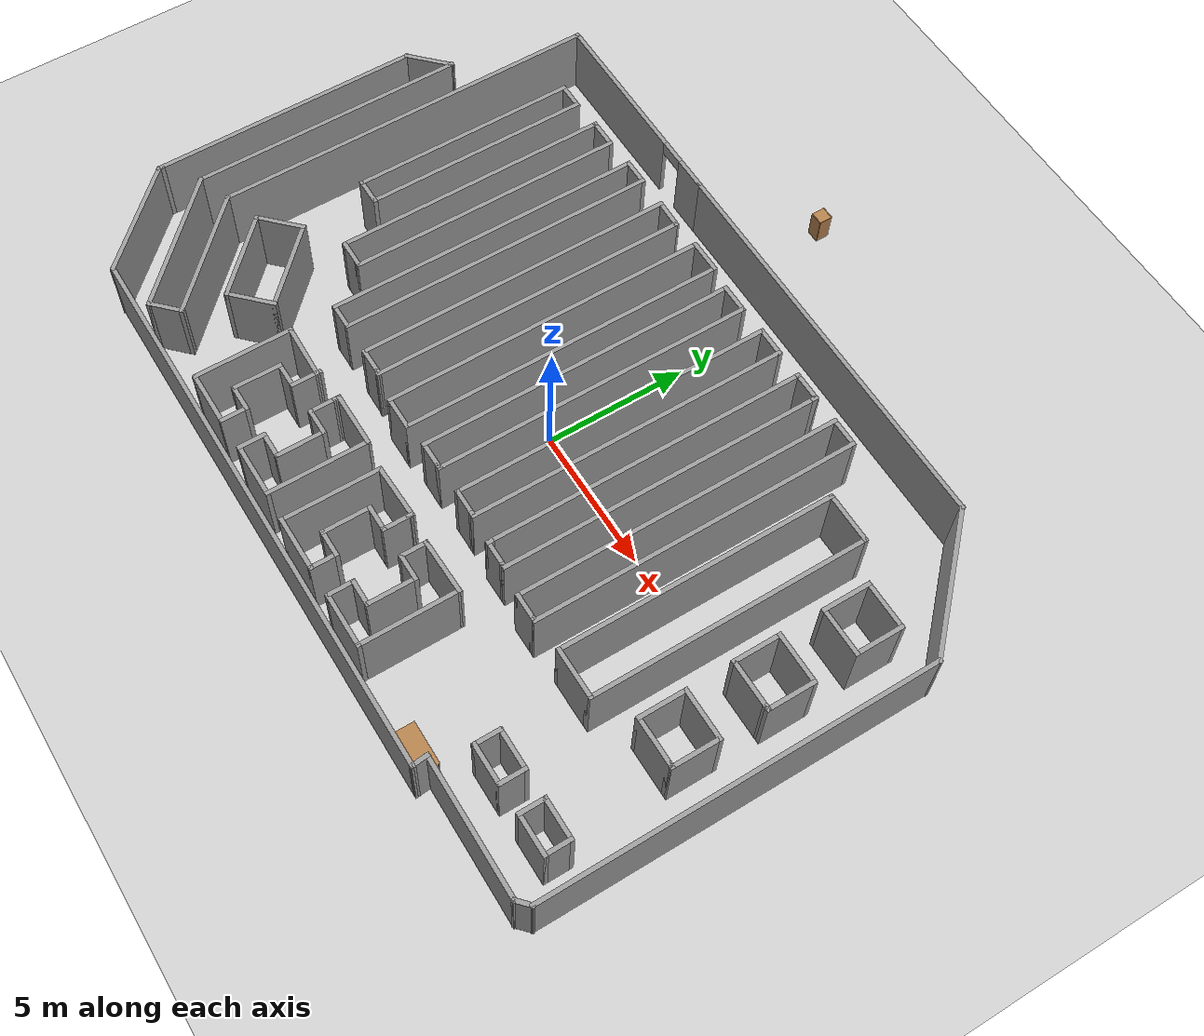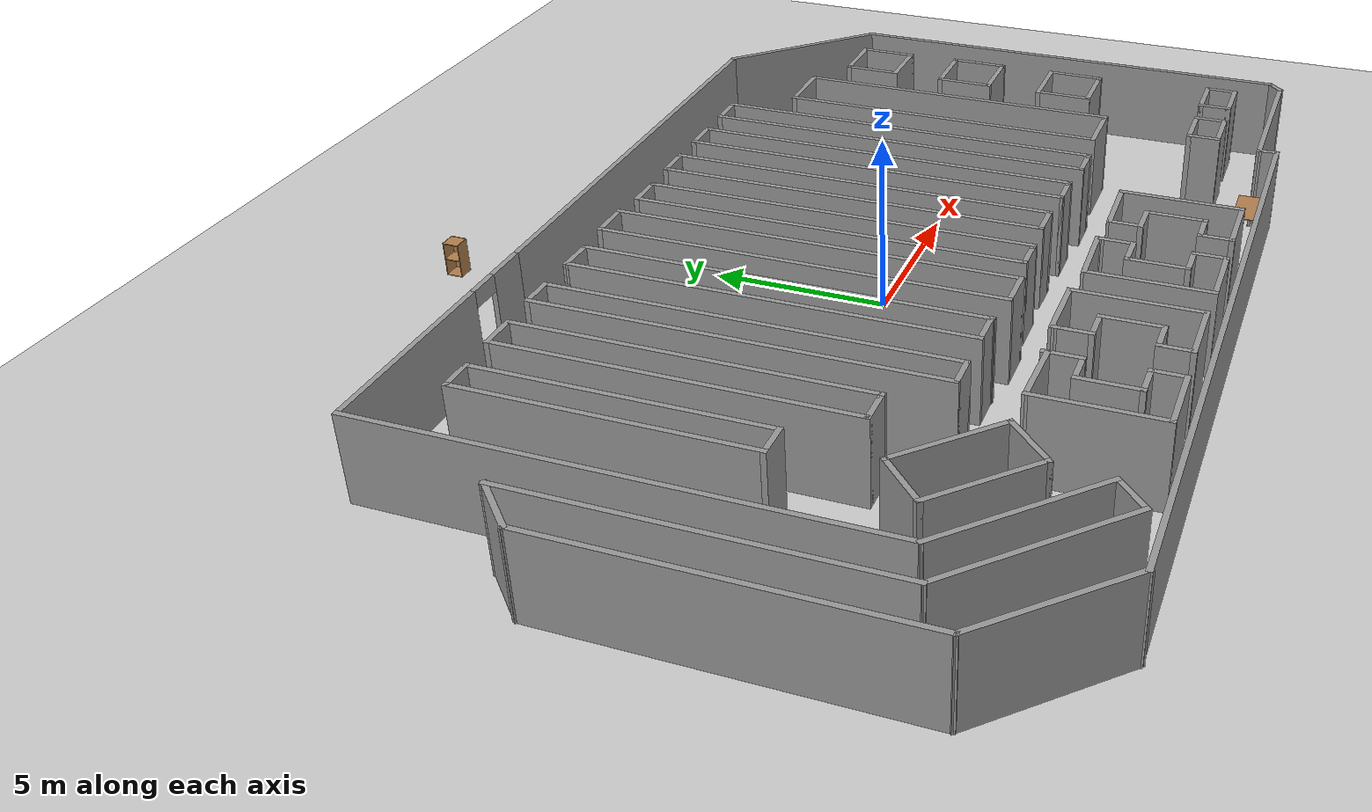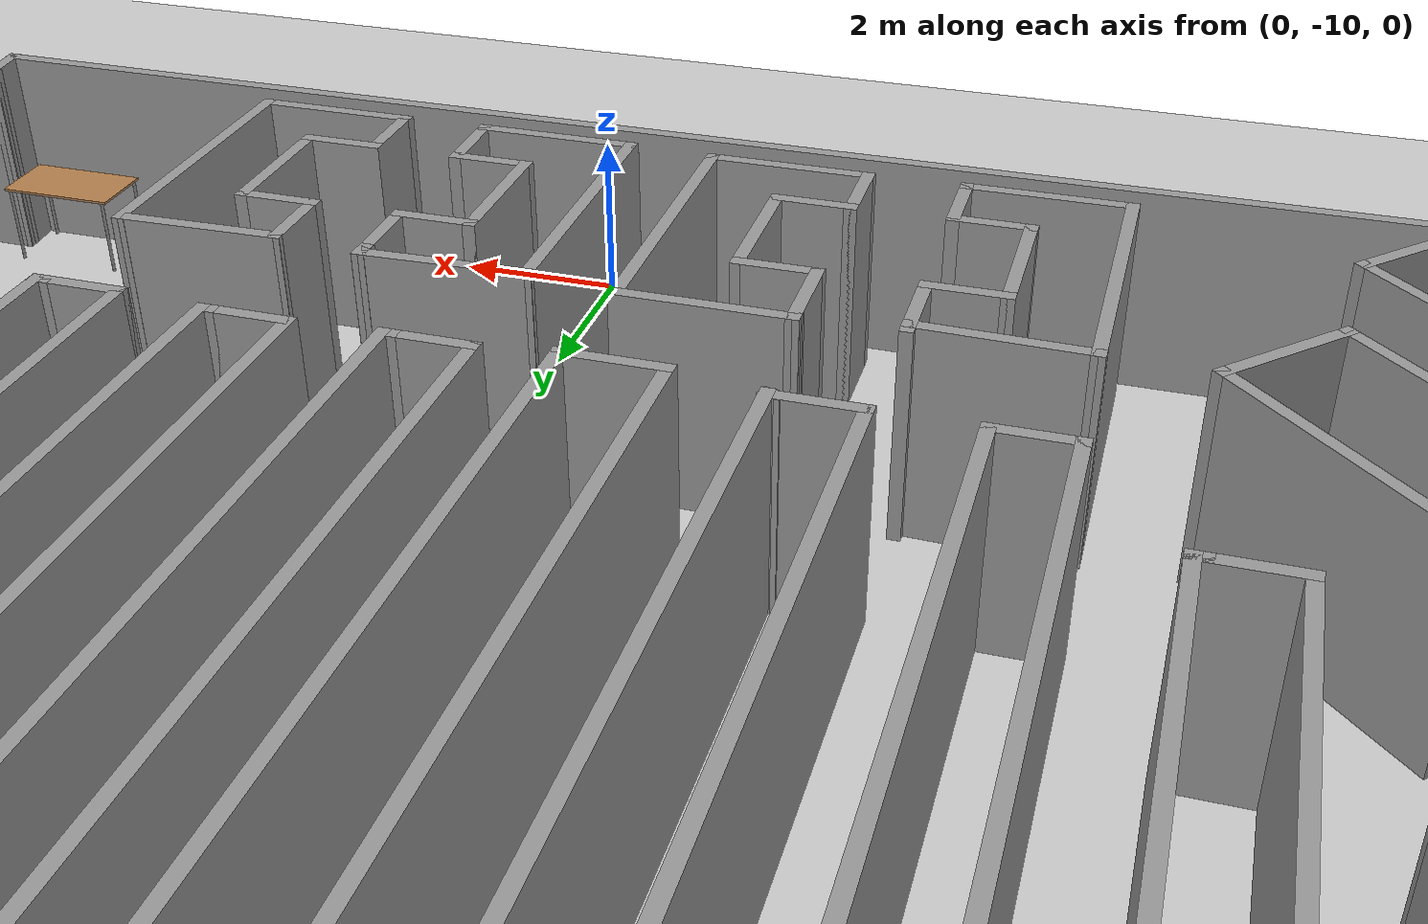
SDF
<sdf version="1.7">
 <world name="default">
  <light name="sun" type="directional">
   <pose>0 0 10 0 -0 0</pose>
   <diffuse>0.8 0.8 0.8 1</diffuse>
   <specular>0.2 0.2 0.2 1</specular>
   <attenuation>
    <range>1000</range>
    <constant>0.9</constant>
    <linear>0.01</linear>
    <quadratic>0.001</quadratic>
   </attenuation>
   <direction>-0.5 0.1 -0.9</direction>
   <spot><inner_angle>0</inner_angle><outer_angle>0</outer_angle><falloff>0</falloff></spot>
  </light>
  <model name="ground_plane">
   <static>1</static>
   <link name="link">
    <collision name="collision">
     <geometry><plane><normal>0 0 1</normal><size>100 100</size></plane></geometry>
     <surface><friction><ode><mu>100</mu><mu2>50</mu2></ode></friction></surface>
    </collision>
    <visual name="visual">
     <cast_shadows>0</cast_shadows>
     <geometry><plane><normal>0 0 1</normal><size>100 100</size></plane></geometry>
     <material>
      <script><uri>file://media/materials/scripts/gazebo.material</uri><name>Gazebo/Grey</name></script>
     </material>
    </visual>
   </link>
  </model>
  <gravity>0 0 -9.8</gravity>
  <magnetic_field>6e-06 2.3e-05 -4.2e-05</magnetic_field>
  <atmosphere type="adiabatic"/>
  <physics type="ode">
   <max_step_size>0.001</max_step_size>
   <real_time_factor>1</real_time_factor>
   <real_time_update_rate>1000</real_time_update_rate>
  </physics>
  <scene><ambient>0.4 0.4 0.4 1</ambient><background>0.7 0.7 0.7 1</background><shadows>1</shadows></scene>
  <audio><device>default</device></audio>
  <spherical_coordinates>
   <surface_model>EARTH_WGS84</surface_model>
   <latitude_deg>0</latitude_deg>
   <longitude_deg>0</longitude_deg>
   <elevation>0</elevation>
   <heading_deg>0</heading_deg>
  </spherical_coordinates>
  <model name="walls_market_g1">
   <pose>-0.66394 -0.44435 0 0 -0 0</pose>
   <link name="Wall_10">
    <pose>-7.72175 9.01697 0 0 -0 3.14159</pose>
    <visual name="Wall_10_Visual_0">
     <pose>-3.2754 0 1.25 0 -0 0</pose>
     <geometry><box><size>1.1992 0.15 2.5</size></box></geometry>
     <material>
      <script><uri>file://media/materials/scripts/gazebo.material</uri><name>Gazebo/Grey</name></script>
      <ambient>1 1 1 1</ambient>
     </material>
     <meta><layer>0</layer></meta>
    </visual>
    <collision name="Wall_10_Collision_0">
     <geometry><box><size>1.1992 0.15 2.5</size></box></geometry>
     <pose>-3.2754 0 1.25 0 -0 0</pose>
    </collision>
    <visual name="Wall_10_Visual_1">
     <pose>1.0496 0 1.25 0 -0 0</pose>
     <geometry><box><size>5.65081 0.15 2.5</size></box></geometry>
     <material>
      <script><uri>file://media/materials/scripts/gazebo.material</uri><name>Gazebo/Grey</name></script>
      <ambient>1 1 1 1</ambient>
     </material>
     <meta><layer>0</layer></meta>
    </visual>
    <collision name="Wall_10_Collision_1">
     <geometry><box><size>5.65081 0.15 2.5</size></box></geometry>
     <pose>1.0496 0 1.25 0 -0 0</pose>
    </collision>
    <visual name="Wall_10_Visual_2">
     <pose>-2.2258 0 2.25 0 -0 0</pose>
     <geometry><box><size>0.9 0.15 0.5</size></box></geometry>
     <material>
      <script><uri>file://media/materials/scripts/gazebo.material</uri><name>Gazebo/Grey</name></script>
      <ambient>1 1 1 1</ambient>
     </material>
     <meta><layer>0</layer></meta>
    </visual>
    <collision name="Wall_10_Collision_2">
     <geometry><box><size>0.9 0.15 0.5</size></box></geometry>
     <pose>-2.2258 0 2.25 0 -0 0</pose>
    </collision>
   </link>
   <link name="Wall_100">
    <collision name="Wall_100_Collision">
     <geometry><box><size>1.85 0.15 2.5</size></box></geometry>
     <pose>0 0 1.25 0 -0 0</pose>
    </collision>
    <visual name="Wall_100_Visual">
     <pose>0 0 1.25 0 -0 0</pose>
     <geometry><box><size>1.85 0.15 2.5</size></box></geometry>
     <material>
      <script><uri>file://media/materials/scripts/gazebo.material</uri><name>Gazebo/Grey</name></script>
      <ambient>1 1 1 1</ambient>
     </material>
     <meta><layer>0</layer></meta>
    </visual>
    <pose>11.6346 -1.28134 0 0 -0 3.14159</pose>
   </link>
   <link name="Wall_102">
    <collision name="Wall_102_Collision">
     <geometry><box><size>3.5 0.15 2.5</size></box></geometry>
     <pose>0 0 1.25 0 -0 0</pose>
    </collision>
    <visual name="Wall_102_Visual">
     <pose>0 0 1.25 0 -0 0</pose>
     <geometry><box><size>3.5 0.15 2.5</size></box></geometry>
     <material>
      <script><uri>file://media/materials/scripts/gazebo.material</uri><name>Gazebo/Grey</name></script>
      <ambient>1 1 1 1</ambient>
     </material>
     <meta><layer>0</layer></meta>
    </visual>
    <pose>-5.82694 -6.89416 0 0 -0 -1.5708</pose>
   </link>
   <link name="Wall_103">
    <collision name="Wall_103_Collision">
     <geometry><box><size>2 0.15 2.5</size></box></geometry>
     <pose>0 0 1.25 0 -0 0</pose>
    </collision>
    <visual name="Wall_103_Visual">
     <pose>0 0 1.25 0 -0 0</pose>
     <geometry><box><size>2 0.15 2.5</size></box></geometry>
     <material>
      <script><uri>file://media/materials/scripts/gazebo.material</uri><name>Gazebo/Grey</name></script>
      <ambient>1 1 1 1</ambient>
     </material>
     <meta><layer>0</layer></meta>
    </visual>
    <pose>-4.90194 -8.56916 0 0 -0 0</pose>
   </link>
   <link name="Wall_104">
    <collision name="Wall_104_Collision">
     <geometry><box><size>1 0.15 2.5</size></box></geometry>
     <pose>0 0 1.25 0 -0 0</pose>
    </collision>
    <visual name="Wall_104_Visual">
     <pose>0 0 1.25 0 -0 0</pose>
     <geometry><box><size>1 0.15 2.5</size></box></geometry>
     <material>
      <script><uri>file://media/materials/scripts/gazebo.material</uri><name>Gazebo/Grey</name></script>
      <ambient>1 1 1 1</ambient>
     </material>
     <meta><layer>0</layer></meta>
    </visual>
    <pose>-3.97694 -8.14416 0 0 -0 1.5708</pose>
   </link>
   <link name="Wall_105">
    <collision name="Wall_105_Collision">
     <geometry><box><size>1 0.15 2.5</size></box></geometry>
     <pose>0 0 1.25 0 -0 0</pose>
    </collision>
    <visual name="Wall_105_Visual">
     <pose>0 0 1.25 0 -0 0</pose>
     <geometry><box><size>1 0.15 2.5</size></box></geometry>
     <material>
      <script><uri>file://media/materials/scripts/gazebo.material</uri><name>Gazebo/Grey</name></script>
      <ambient>1 1 1 1</ambient>
     </material>
     <meta><layer>0</layer></meta>
    </visual>
    <pose>-4.40194 -7.71916 0 0 -0 3.14159</pose>
   </link>
   <link name="Wall_106">
    <collision name="Wall_106_Collision">
     <geometry><box><size>1.75 0.15 2.5</size></box></geometry>
     <pose>0 0 1.25 0 -0 0</pose>
    </collision>
    <visual name="Wall_106_Visual">
     <pose>0 0 1.25 0 -0 0</pose>
     <geometry><box><size>1.75 0.15 2.5</size></box></geometry>
     <material>
      <script><uri>file://media/materials/scripts/gazebo.material</uri><name>Gazebo/Grey</name></script>
      <ambient>1 1 1 1</ambient>
     </material>
     <meta><layer>0</layer></meta>
    </visual>
    <pose>-4.82694 -6.91916 0 0 -0 1.5708</pose>
   </link>
   <link name="Wall_107">
    <collision name="Wall_107_Collision">
     <geometry><box><size>1 0.15 2.5</size></box></geometry>
     <pose>0 0 1.25 0 -0 0</pose>
    </collision>
    <visual name="Wall_107_Visual">
     <pose>0 0 1.25 0 -0 0</pose>
     <geometry><box><size>1 0.15 2.5</size></box></geometry>
     <material>
      <script><uri>file://media/materials/scripts/gazebo.material</uri><name>Gazebo/Grey</name></script>
      <ambient>1 1 1 1</ambient>
     </material>
     <meta><layer>0</layer></meta>
    </visual>
    <pose>-4.40194 -6.11916 0 0 -0 0</pose>
   </link>
   <link name="Wall_108">
    <collision name="Wall_108_Collision">
     <geometry><box><size>1 0.15 2.5</size></box></geometry>
     <pose>0 0 1.25 0 -0 0</pose>
    </collision>
    <visual name="Wall_108_Visual">
     <pose>0 0 1.25 0 -0 0</pose>
     <geometry><box><size>1 0.15 2.5</size></box></geometry>
     <material>
      <script><uri>file://media/materials/scripts/gazebo.material</uri><name>Gazebo/Grey</name></script>
      <ambient>1 1 1 1</ambient>
     </material>
     <meta><layer>0</layer></meta>
    </visual>
    <pose>-3.97694 -5.69416 0 0 -0 1.5708</pose>
   </link>
   <link name="Wall_109">
    <collision name="Wall_109_Collision">
     <geometry><box><size>2.00068 0.15 2.5</size></box></geometry>
     <pose>0 0 1.25 0 -0 0</pose>
    </collision>
    <visual name="Wall_109_Visual">
     <pose>0 0 1.25 0 -0 0</pose>
     <geometry><box><size>2.00068 0.15 2.5</size></box></geometry>
     <material>
      <script><uri>file://media/materials/scripts/gazebo.material</uri><name>Gazebo/Grey</name></script>
      <ambient>1 1 1 1</ambient>
     </material>
     <meta><layer>0</layer></meta>
    </visual>
    <pose>-4.90194 -5.24416 0 0 -0 3.11457</pose>
   </link>
   <link name="Wall_11">
    <collision name="Wall_11_Collision">
     <geometry><box><size>13.75 0.15 2.5</size></box></geometry>
     <pose>0 0 1.25 0 -0 0</pose>
    </collision>
    <visual name="Wall_11_Visual">
     <pose>0 0 1.25 0 -0 0</pose>
     <geometry><box><size>13.75 0.15 2.5</size></box></geometry>
     <material>
      <script><uri>file://media/materials/scripts/gazebo.material</uri><name>Gazebo/Grey</name></script>
      <ambient>1 1 1 1</ambient>
     </material>
     <meta><layer>0</layer></meta>
    </visual>
    <pose>-11.5218 2.21697 0 0 -0 -1.5708</pose>
   </link>
   <link name="Wall_111">
    <collision name="Wall_111_Collision">
     <geometry><box><size>1 0.15 2.5</size></box></geometry>
     <pose>0 0 1.25 0 -0 0</pose>
    </collision>
    <visual name="Wall_111_Visual">
     <pose>0 0 1.25 0 -0 0</pose>
     <geometry><box><size>1 0.15 2.5</size></box></geometry>
     <material>
      <script><uri>file://media/materials/scripts/gazebo.material</uri><name>Gazebo/Grey</name></script>
      <ambient>1 1 1 1</ambient>
     </material>
     <meta><layer>0</layer></meta>
    </visual>
    <pose>-3.97694 -5.69416 0 0 -0 1.5708</pose>
   </link>
   <link name="Wall_112">
    <collision name="Wall_112_Collision">
     <geometry><box><size>0.25 0.15 2.5</size></box></geometry>
     <pose>0 0 1.25 0 -0 0</pose>
    </collision>
    <visual name="Wall_112_Visual">
     <pose>0 0 1.25 0 -0 0</pose>
     <geometry><box><size>0.25 0.15 2.5</size></box></geometry>
     <material>
      <script><uri>file://media/materials/scripts/gazebo.material</uri><name>Gazebo/Grey</name></script>
      <ambient>1 1 1 1</ambient>
     </material>
     <meta><layer>0</layer></meta>
    </visual>
    <pose>-3.97694 -5.21916 0 0 -0 1.5708</pose>
   </link>
   <link name="Wall_114">
    <collision name="Wall_114_Collision">
     <geometry><box><size>3.5 0.15 2.5</size></box></geometry>
     <pose>0 0 1.25 0 -0 0</pose>
    </collision>
    <visual name="Wall_114_Visual">
     <pose>0 0 1.25 0 -0 0</pose>
     <geometry><box><size>3.5 0.15 2.5</size></box></geometry>
     <material>
      <script><uri>file://media/materials/scripts/gazebo.material</uri><name>Gazebo/Grey</name></script>
      <ambient>1 1 1 1</ambient>
     </material>
     <meta><layer>0</layer></meta>
    </visual>
    <pose>-0.99694 -6.85966 0 0 -0 -1.5708</pose>
   </link>
   <link name="Wall_115">
    <collision name="Wall_115_Collision">
     <geometry><box><size>2 0.15 2.5</size></box></geometry>
     <pose>0 0 1.25 0 -0 0</pose>
    </collision>
    <visual name="Wall_115_Visual">
     <pose>0 0 1.25 0 -0 0</pose>
     <geometry><box><size>2 0.15 2.5</size></box></geometry>
     <material>
      <script><uri>file://media/materials/scripts/gazebo.material</uri><name>Gazebo/Grey</name></script>
      <ambient>1 1 1 1</ambient>
     </material>
     <meta><layer>0</layer></meta>
    </visual>
    <pose>-1.92194 -8.53466 0 0 -0 3.14159</pose>
   </link>
   <link name="Wall_116">
    <collision name="Wall_116_Collision">
     <geometry><box><size>1 0.15 2.5</size></box></geometry>
     <pose>0 0 1.25 0 -0 0</pose>
    </collision>
    <visual name="Wall_116_Visual">
     <pose>0 0 1.25 0 -0 0</pose>
     <geometry><box><size>1 0.15 2.5</size></box></geometry>
     <material>
      <script><uri>file://media/materials/scripts/gazebo.material</uri><name>Gazebo/Grey</name></script>
      <ambient>1 1 1 1</ambient>
     </material>
     <meta><layer>0</layer></meta>
    </visual>
    <pose>-2.84694 -8.10966 0 0 -0 1.5708</pose>
   </link>
   <link name="Wall_117">
    <collision name="Wall_117_Collision">
     <geometry><box><size>1 0.15 2.5</size></box></geometry>
     <pose>0 0 1.25 0 -0 0</pose>
    </collision>
    <visual name="Wall_117_Visual">
     <pose>0 0 1.25 0 -0 0</pose>
     <geometry><box><size>1 0.15 2.5</size></box></geometry>
     <material>
      <script><uri>file://media/materials/scripts/gazebo.material</uri><name>Gazebo/Grey</name></script>
      <ambient>1 1 1 1</ambient>
     </material>
     <meta><layer>0</layer></meta>
    </visual>
    <pose>-2.42194 -7.68466 0 0 -0 0</pose>
   </link>
   <link name="Wall_118">
    <collision name="Wall_118_Collision">
     <geometry><box><size>1.75 0.15 2.5</size></box></geometry>
     <pose>0 0 1.25 0 -0 0</pose>
    </collision>
    <visual name="Wall_118_Visual">
     <pose>0 0 1.25 0 -0 0</pose>
     <geometry><box><size>1.75 0.15 2.5</size></box></geometry>
     <material>
      <script><uri>file://media/materials/scripts/gazebo.material</uri><name>Gazebo/Grey</name></script>
      <ambient>1 1 1 1</ambient>
     </material>
     <meta><layer>0</layer></meta>
    </visual>
    <pose>-1.99694 -6.88466 0 0 -0 1.5708</pose>
   </link>
   <link name="Wall_119">
    <collision name="Wall_119_Collision">
     <geometry><box><size>1 0.15 2.5</size></box></geometry>
     <pose>0 0 1.25 0 -0 0</pose>
    </collision>
    <visual name="Wall_119_Visual">
     <pose>0 0 1.25 0 -0 0</pose>
     <geometry><box><size>1 0.15 2.5</size></box></geometry>
     <material>
      <script><uri>file://media/materials/scripts/gazebo.material</uri><name>Gazebo/Grey</name></script>
      <ambient>1 1 1 1</ambient>
     </material>
     <meta><layer>0</layer></meta>
    </visual>
    <pose>-2.42194 -6.08466 0 0 -0 3.14159</pose>
   </link>
   <link name="Wall_12">
    <collision name="Wall_12_Collision">
     <geometry><box><size>4.75 0.15 2.5</size></box></geometry>
     <pose>0 0 1.25 0 -0 0</pose>
    </collision>
    <visual name="Wall_12_Visual">
     <pose>0 0 1.25 0 -0 0</pose>
     <geometry><box><size>4.75 0.15 2.5</size></box></geometry>
     <material>
      <script><uri>file://media/materials/scripts/gazebo.material</uri><name>Gazebo/Grey</name></script>
      <ambient>1 1 1 1</ambient>
     </material>
     <meta><layer>0</layer></meta>
    </visual>
    <pose>-9.89541 -6.20938 0 0 -0 -0.785398</pose>
   </link>
   <link name="Wall_120">
    <collision name="Wall_120_Collision">
     <geometry><box><size>1 0.15 2.5</size></box></geometry>
     <pose>0 0 1.25 0 -0 0</pose>
    </collision>
    <visual name="Wall_120_Visual">
     <pose>0 0 1.25 0 -0 0</pose>
     <geometry><box><size>1 0.15 2.5</size></box></geometry>
     <material>
      <script><uri>file://media/materials/scripts/gazebo.material</uri><name>Gazebo/Grey</name></script>
      <ambient>1 1 1 1</ambient>
     </material>
     <meta><layer>0</layer></meta>
    </visual>
    <pose>-2.84694 -5.65966 0 0 -0 1.5708</pose>
   </link>
   <link name="Wall_121">
    <collision name="Wall_121_Collision">
     <geometry><box><size>0.292008 0.15 2.5</size></box></geometry>
     <pose>0 0 1.25 0 -0 0</pose>
    </collision>
    <visual name="Wall_121_Visual">
     <pose>0 0 1.25 0 -0 0</pose>
     <geometry><box><size>0.292008 0.15 2.5</size></box></geometry>
     <material>
      <script><uri>file://media/materials/scripts/gazebo.material</uri><name>Gazebo/Grey</name></script>
      <ambient>1 1 1 1</ambient>
     </material>
     <meta><layer>0</layer></meta>
    </visual>
    <pose>-2.84769 -5.16366 0 0 -0 1.58136</pose>
   </link>
   <link name="Wall_122">
    <collision name="Wall_122_Collision">
     <geometry><box><size>2 0.15 2.5</size></box></geometry>
     <pose>0 0 1.25 0 -0 0</pose>
    </collision>
    <visual name="Wall_122_Visual">
     <pose>0 0 1.25 0 -0 0</pose>
     <geometry><box><size>2 0.15 2.5</size></box></geometry>
     <material>
      <script><uri>file://media/materials/scripts/gazebo.material</uri><name>Gazebo/Grey</name></script>
      <ambient>1 1 1 1</ambient>
     </material>
     <meta><layer>0</layer></meta>
    </visual>
    <pose>-1.92344 -5.09266 0 0 -0 0</pose>
   </link>
   <link name="Wall_124">
    <collision name="Wall_124_Collision">
     <geometry><box><size>3.5 0.15 2.5</size></box></geometry>
     <pose>0 0 1.25 0 -0 0</pose>
    </collision>
    <visual name="Wall_124_Visual">
     <pose>0 0 1.25 0 -0 0</pose>
     <geometry><box><size>3.5 0.15 2.5</size></box></geometry>
     <material>
      <script><uri>file://media/materials/scripts/gazebo.material</uri><name>Gazebo/Grey</name></script>
      <ambient>1 1 1 1</ambient>
     </material>
     <meta><layer>0</layer></meta>
    </visual>
    <pose>0.02656 -6.90566 0 0 -0 -1.5708</pose>
   </link>
   <link name="Wall_125">
    <collision name="Wall_125_Collision">
     <geometry><box><size>2 0.15 2.5</size></box></geometry>
     <pose>0 0 1.25 0 -0 0</pose>
    </collision>
    <visual name="Wall_125_Visual">
     <pose>0 0 1.25 0 -0 0</pose>
     <geometry><box><size>2 0.15 2.5</size></box></geometry>
     <material>
      <script><uri>file://media/materials/scripts/gazebo.material</uri><name>Gazebo/Grey</name></script>
      <ambient>1 1 1 1</ambient>
     </material>
     <meta><layer>0</layer></meta>
    </visual>
    <pose>0.95156 -8.58066 0 0 -0 0</pose>
   </link>
   <link name="Wall_126">
    <collision name="Wall_126_Collision">
     <geometry><box><size>1 0.15 2.5</size></box></geometry>
     <pose>0 0 1.25 0 -0 0</pose>
    </collision>
    <visual name="Wall_126_Visual">
     <pose>0 0 1.25 0 -0 0</pose>
     <geometry><box><size>1 0.15 2.5</size></box></geometry>
     <material>
      <script><uri>file://media/materials/scripts/gazebo.material</uri><name>Gazebo/Grey</name></script>
      <ambient>1 1 1 1</ambient>
     </material>
     <meta><layer>0</layer></meta>
    </visual>
    <pose>1.87656 -8.15566 0 0 -0 1.5708</pose>
   </link>
   <link name="Wall_127">
    <collision name="Wall_127_Collision">
     <geometry><box><size>1 0.15 2.5</size></box></geometry>
     <pose>0 0 1.25 0 -0 0</pose>
    </collision>
    <visual name="Wall_127_Visual">
     <pose>0 0 1.25 0 -0 0</pose>
     <geometry><box><size>1 0.15 2.5</size></box></geometry>
     <material>
      <script><uri>file://media/materials/scripts/gazebo.material</uri><name>Gazebo/Grey</name></script>
      <ambient>1 1 1 1</ambient>
     </material>
     <meta><layer>0</layer></meta>
    </visual>
    <pose>1.45156 -7.73066 0 0 -0 3.14159</pose>
   </link>
   <link name="Wall_128">
    <collision name="Wall_128_Collision">
     <geometry><box><size>1.75 0.15 2.5</size></box></geometry>
     <pose>0 0 1.25 0 -0 0</pose>
    </collision>
    <visual name="Wall_128_Visual">
     <pose>0 0 1.25 0 -0 0</pose>
     <geometry><box><size>1.75 0.15 2.5</size></box></geometry>
     <material>
      <script><uri>file://media/materials/scripts/gazebo.material</uri><name>Gazebo/Grey</name></script>
      <ambient>1 1 1 1</ambient>
     </material>
     <meta><layer>0</layer></meta>
    </visual>
    <pose>1.02656 -6.93066 0 0 -0 1.5708</pose>
   </link>
   <link name="Wall_129">
    <collision name="Wall_129_Collision">
     <geometry><box><size>1 0.15 2.5</size></box></geometry>
     <pose>0 0 1.25 0 -0 0</pose>
    </collision>
    <visual name="Wall_129_Visual">
     <pose>0 0 1.25 0 -0 0</pose>
     <geometry><box><size>1 0.15 2.5</size></box></geometry>
     <material>
      <script><uri>file://media/materials/scripts/gazebo.material</uri><name>Gazebo/Grey</name></script>
      <ambient>1 1 1 1</ambient>
     </material>
     <meta><layer>0</layer></meta>
    </visual>
    <pose>1.45156 -6.13066 0 0 -0 0</pose>
   </link>
   <link name="Wall_13">
    <collision name="Wall_13_Collision">
     <geometry><box><size>1.25 0.15 2.5</size></box></geometry>
     <pose>0 0 1.25 0 -0 0</pose>
    </collision>
    <visual name="Wall_13_Visual">
     <pose>0 0 1.25 0 -0 0</pose>
     <geometry><box><size>1.25 0.15 2.5</size></box></geometry>
     <material>
      <script><uri>file://media/materials/scripts/gazebo.material</uri><name>Gazebo/Grey</name></script>
      <ambient>1 1 1 1</ambient>
     </material>
     <meta><layer>0</layer></meta>
    </visual>
    <pose>-8.65797 -8.22463 0 0 -0 -2.35619</pose>
   </link>
   <link name="Wall_130">
    <collision name="Wall_130_Collision">
     <geometry><box><size>1 0.15 2.5</size></box></geometry>
     <pose>0 0 1.25 0 -0 0</pose>
    </collision>
    <visual name="Wall_130_Visual">
     <pose>0 0 1.25 0 -0 0</pose>
     <geometry><box><size>1 0.15 2.5</size></box></geometry>
     <material>
      <script><uri>file://media/materials/scripts/gazebo.material</uri><name>Gazebo/Grey</name></script>
      <ambient>1 1 1 1</ambient>
     </material>
     <meta><layer>0</layer></meta>
    </visual>
    <pose>1.87656 -5.70566 0 0 -0 1.5708</pose>
   </link>
   <link name="Wall_131">
    <collision name="Wall_131_Collision">
     <geometry><box><size>0.25751 0.15 2.5</size></box></geometry>
     <pose>0 0 1.25 0 -0 0</pose>
    </collision>
    <visual name="Wall_131_Visual">
     <pose>0 0 1.25 0 -0 0</pose>
     <geometry><box><size>0.25751 0.15 2.5</size></box></geometry>
     <material>
      <script><uri>file://media/materials/scripts/gazebo.material</uri><name>Gazebo/Grey</name></script>
      <ambient>1 1 1 1</ambient>
     </material>
     <meta><layer>0</layer></meta>
    </visual>
    <pose>1.87731 -5.22691 0 0 -0 1.55684</pose>
   </link>
   <link name="Wall_132">
    <collision name="Wall_132_Collision">
     <geometry><box><size>2.00239 0.15 2.5</size></box></geometry>
     <pose>0 0 1.25 0 -0 0</pose>
    </collision>
    <visual name="Wall_132_Visual">
     <pose>0 0 1.25 0 -0 0</pose>
     <geometry><box><size>2.00239 0.15 2.5</size></box></geometry>
     <material>
      <script><uri>file://media/materials/scripts/gazebo.material</uri><name>Gazebo/Grey</name></script>
      <ambient>1 1 1 1</ambient>
     </material>
     <meta><layer>0</layer></meta>
    </visual>
    <pose>0.95231 -5.20191 0 0 -0 -3.11055</pose>
   </link>
   <link name="Wall_134">
    <collision name="Wall_134_Collision">
     <geometry><box><size>3.5 0.15 2.5</size></box></geometry>
     <pose>0 0 1.25 0 -0 0</pose>
    </collision>
    <visual name="Wall_134_Visual">
     <pose>0 0 1.25 0 -0 0</pose>
     <geometry><box><size>3.5 0.15 2.5</size></box></geometry>
     <material>
      <script><uri>file://media/materials/scripts/gazebo.material</uri><name>Gazebo/Grey</name></script>
      <ambient>1 1 1 1</ambient>
     </material>
     <meta><layer>0</layer></meta>
    </visual>
    <pose>4.76456 -6.89416 0 0 -0 -1.5708</pose>
   </link>
   <link name="Wall_135">
    <collision name="Wall_135_Collision">
     <geometry><box><size>2 0.15 2.5</size></box></geometry>
     <pose>0 0 1.25 0 -0 0</pose>
    </collision>
    <visual name="Wall_135_Visual">
     <pose>0 0 1.25 0 -0 0</pose>
     <geometry><box><size>2 0.15 2.5</size></box></geometry>
     <material>
      <script><uri>file://media/materials/scripts/gazebo.material</uri><name>Gazebo/Grey</name></script>
      <ambient>1 1 1 1</ambient>
     </material>
     <meta><layer>0</layer></meta>
    </visual>
    <pose>3.83956 -8.56916 0 0 -0 3.14159</pose>
   </link>
   <link name="Wall_136">
    <collision name="Wall_136_Collision">
     <geometry><box><size>1 0.15 2.5</size></box></geometry>
     <pose>0 0 1.25 0 -0 0</pose>
    </collision>
    <visual name="Wall_136_Visual">
     <pose>0 0 1.25 0 -0 0</pose>
     <geometry><box><size>1 0.15 2.5</size></box></geometry>
     <material>
      <script><uri>file://media/materials/scripts/gazebo.material</uri><name>Gazebo/Grey</name></script>
      <ambient>1 1 1 1</ambient>
     </material>
     <meta><layer>0</layer></meta>
    </visual>
    <pose>2.91456 -8.14416 0 0 -0 1.5708</pose>
   </link>
   <link name="Wall_137">
    <collision name="Wall_137_Collision">
     <geometry><box><size>1 0.15 2.5</size></box></geometry>
     <pose>0 0 1.25 0 -0 0</pose>
    </collision>
    <visual name="Wall_137_Visual">
     <pose>0 0 1.25 0 -0 0</pose>
     <geometry><box><size>1 0.15 2.5</size></box></geometry>
     <material>
      <script><uri>file://media/materials/scripts/gazebo.material</uri><name>Gazebo/Grey</name></script>
      <ambient>1 1 1 1</ambient>
     </material>
     <meta><layer>0</layer></meta>
    </visual>
    <pose>3.33956 -7.71916 0 0 -0 0</pose>
   </link>
   <link name="Wall_138">
    <collision name="Wall_138_Collision">
     <geometry><box><size>1.75 0.15 2.5</size></box></geometry>
     <pose>0 0 1.25 0 -0 0</pose>
    </collision>
    <visual name="Wall_138_Visual">
     <pose>0 0 1.25 0 -0 0</pose>
     <geometry><box><size>1.75 0.15 2.5</size></box></geometry>
     <material>
      <script><uri>file://media/materials/scripts/gazebo.material</uri><name>Gazebo/Grey</name></script>
      <ambient>1 1 1 1</ambient>
     </material>
     <meta><layer>0</layer></meta>
    </visual>
    <pose>3.76456 -6.91916 0 0 -0 1.5708</pose>
   </link>
   <link name="Wall_139">
    <collision name="Wall_139_Collision">
     <geometry><box><size>1 0.15 2.5</size></box></geometry>
     <pose>0 0 1.25 0 -0 0</pose>
    </collision>
    <visual name="Wall_139_Visual">
     <pose>0 0 1.25 0 -0 0</pose>
     <geometry><box><size>1 0.15 2.5</size></box></geometry>
     <material>
      <script><uri>file://media/materials/scripts/gazebo.material</uri><name>Gazebo/Grey</name></script>
      <ambient>1 1 1 1</ambient>
     </material>
     <meta><layer>0</layer></meta>
    </visual>
    <pose>3.33956 -6.11916 0 0 -0 3.14159</pose>
   </link>
   <link name="Wall_14">
    <collision name="Wall_14_Collision">
     <geometry><box><size>5.25 0.15 2.5</size></box></geometry>
     <pose>0 0 1.25 0 -0 0</pose>
    </collision>
    <visual name="Wall_14_Visual">
     <pose>0 0 1.25 0 -0 0</pose>
     <geometry><box><size>5.25 0.15 2.5</size></box></geometry>
     <material>
      <script><uri>file://media/materials/scripts/gazebo.material</uri><name>Gazebo/Grey</name></script>
      <ambient>1 1 1 1</ambient>
     </material>
     <meta><layer>0</layer></meta>
    </visual>
    <pose>-10.85 -6.81042 0 0 -0 2.35619</pose>
   </link>
   <link name="Wall_140">
    <collision name="Wall_140_Collision">
     <geometry><box><size>1 0.15 2.5</size></box></geometry>
     <pose>0 0 1.25 0 -0 0</pose>
    </collision>
    <visual name="Wall_140_Visual">
     <pose>0 0 1.25 0 -0 0</pose>
     <geometry><box><size>1 0.15 2.5</size></box></geometry>
     <material>
      <script><uri>file://media/materials/scripts/gazebo.material</uri><name>Gazebo/Grey</name></script>
      <ambient>1 1 1 1</ambient>
     </material>
     <meta><layer>0</layer></meta>
    </visual>
    <pose>2.91456 -5.69416 0 0 -0 1.5708</pose>
   </link>
   <link name="Wall_141">
    <collision name="Wall_141_Collision">
     <geometry><box><size>2.00068 0.15 2.5</size></box></geometry>
     <pose>0 0 1.25 0 -0 0</pose>
    </collision>
    <visual name="Wall_141_Visual">
     <pose>0 0 1.25 0 -0 0</pose>
     <geometry><box><size>2.00068 0.15 2.5</size></box></geometry>
     <material>
      <script><uri>file://media/materials/scripts/gazebo.material</uri><name>Gazebo/Grey</name></script>
      <ambient>1 1 1 1</ambient>
     </material>
     <meta><layer>0</layer></meta>
    </visual>
    <pose>3.83956 -5.24416 0 0 -0 0.02702</pose>
   </link>
   <link name="Wall_143">
    <collision name="Wall_143_Collision">
     <geometry><box><size>1 0.15 2.5</size></box></geometry>
     <pose>0 0 1.25 0 -0 0</pose>
    </collision>
    <visual name="Wall_143_Visual">
     <pose>0 0 1.25 0 -0 0</pose>
     <geometry><box><size>1 0.15 2.5</size></box></geometry>
     <material>
      <script><uri>file://media/materials/scripts/gazebo.material</uri><name>Gazebo/Grey</name></script>
      <ambient>1 1 1 1</ambient>
     </material>
     <meta><layer>0</layer></meta>
    </visual>
    <pose>9.0747 -6.80653 0 0 -0 -1.5708</pose>
   </link>
   <link name="Wall_144">
    <collision name="Wall_144_Collision">
     <geometry><box><size>1.5 0.15 2.5</size></box></geometry>
     <pose>0 0 1.25 0 -0 0</pose>
    </collision>
    <visual name="Wall_144_Visual">
     <pose>0 0 1.25 0 -0 0</pose>
     <geometry><box><size>1.5 0.15 2.5</size></box></geometry>
     <material>
      <script><uri>file://media/materials/scripts/gazebo.material</uri><name>Gazebo/Grey</name></script>
      <ambient>1 1 1 1</ambient>
     </material>
     <meta><layer>0</layer></meta>
    </visual>
    <pose>9.7497 -7.23153 0 0 -0 0</pose>
   </link>
   <link name="Wall_145">
    <collision name="Wall_145_Collision">
     <geometry><box><size>1 0.15 2.5</size></box></geometry>
     <pose>0 0 1.25 0 -0 0</pose>
    </collision>
    <visual name="Wall_145_Visual">
     <pose>0 0 1.25 0 -0 0</pose>
     <geometry><box><size>1 0.15 2.5</size></box></geometry>
     <material>
      <script><uri>file://media/materials/scripts/gazebo.material</uri><name>Gazebo/Grey</name></script>
      <ambient>1 1 1 1</ambient>
     </material>
     <meta><layer>0</layer></meta>
    </visual>
    <pose>10.4247 -6.80653 0 0 -0 1.5708</pose>
   </link>
   <link name="Wall_146">
    <collision name="Wall_146_Collision">
     <geometry><box><size>1.5 0.15 2.5</size></box></geometry>
     <pose>0 0 1.25 0 -0 0</pose>
    </collision>
    <visual name="Wall_146_Visual">
     <pose>0 0 1.25 0 -0 0</pose>
     <geometry><box><size>1.5 0.15 2.5</size></box></geometry>
     <material>
      <script><uri>file://media/materials/scripts/gazebo.material</uri><name>Gazebo/Grey</name></script>
      <ambient>1 1 1 1</ambient>
     </material>
     <meta><layer>0</layer></meta>
    </visual>
    <pose>9.7497 -6.38153 0 0 -0 3.14159</pose>
   </link>
   <link name="Wall_148">
    <collision name="Wall_148_Collision">
     <geometry><box><size>1 0.15 2.5</size></box></geometry>
     <pose>0 0 1.25 0 -0 0</pose>
    </collision>
    <visual name="Wall_148_Visual">
     <pose>0 0 1.25 0 -0 0</pose>
     <geometry><box><size>1 0.15 2.5</size></box></geometry>
     <material>
      <script><uri>file://media/materials/scripts/gazebo.material</uri><name>Gazebo/Grey</name></script>
      <ambient>1 1 1 1</ambient>
     </material>
     <meta><layer>0</layer></meta>
    </visual>
    <pose>11.4321 -6.77611 0 0 -0 -1.5708</pose>
   </link>
   <link name="Wall_149">
    <collision name="Wall_149_Collision">
     <geometry><box><size>1.5 0.15 2.5</size></box></geometry>
     <pose>0 0 1.25 0 -0 0</pose>
    </collision>
    <visual name="Wall_149_Visual">
     <pose>0 0 1.25 0 -0 0</pose>
     <geometry><box><size>1.5 0.15 2.5</size></box></geometry>
     <material>
      <script><uri>file://media/materials/scripts/gazebo.material</uri><name>Gazebo/Grey</name></script>
      <ambient>1 1 1 1</ambient>
     </material>
     <meta><layer>0</layer></meta>
    </visual>
    <pose>12.1071 -7.20111 0 0 -0 0</pose>
   </link>
   <link name="Wall_15">
    <collision name="Wall_15_Collision">
     <geometry><box><size>9.75 0.15 2.5</size></box></geometry>
     <pose>0 0 1.25 0 -0 0</pose>
    </collision>
    <visual name="Wall_15_Visual">
     <pose>0 0 1.25 0 -0 0</pose>
     <geometry><box><size>9.75 0.15 2.5</size></box></geometry>
     <material>
      <script><uri>file://media/materials/scripts/gazebo.material</uri><name>Gazebo/Grey</name></script>
      <ambient>1 1 1 1</ambient>
     </material>
     <meta><layer>0</layer></meta>
    </visual>
    <pose>-12.6531 -0.207299 0 0 -0 1.5708</pose>
   </link>
   <link name="Wall_150">
    <collision name="Wall_150_Collision">
     <geometry><box><size>1 0.15 2.5</size></box></geometry>
     <pose>0 0 1.25 0 -0 0</pose>
    </collision>
    <visual name="Wall_150_Visual">
     <pose>0 0 1.25 0 -0 0</pose>
     <geometry><box><size>1 0.15 2.5</size></box></geometry>
     <material>
      <script><uri>file://media/materials/scripts/gazebo.material</uri><name>Gazebo/Grey</name></script>
      <ambient>1 1 1 1</ambient>
     </material>
     <meta><layer>0</layer></meta>
    </visual>
    <pose>12.7821 -6.77611 0 0 -0 1.5708</pose>
   </link>
   <link name="Wall_151">
    <collision name="Wall_151_Collision">
     <geometry><box><size>1.5 0.15 2.5</size></box></geometry>
     <pose>0 0 1.25 0 -0 0</pose>
    </collision>
    <visual name="Wall_151_Visual">
     <pose>0 0 1.25 0 -0 0</pose>
     <geometry><box><size>1.5 0.15 2.5</size></box></geometry>
     <material>
      <script><uri>file://media/materials/scripts/gazebo.material</uri><name>Gazebo/Grey</name></script>
      <ambient>1 1 1 1</ambient>
     </material>
     <meta><layer>0</layer></meta>
    </visual>
    <pose>12.1071 -6.35111 0 0 -0 3.14159</pose>
   </link>
   <link name="Wall_16">
    <collision name="Wall_16_Collision">
     <geometry><box><size>1.75 0.15 2.5</size></box></geometry>
     <pose>0 0 1.25 0 -0 0</pose>
    </collision>
    <visual name="Wall_16_Visual">
     <pose>0 0 1.25 0 -0 0</pose>
     <geometry><box><size>1.75 0.15 2.5</size></box></geometry>
     <material>
      <script><uri>file://media/materials/scripts/gazebo.material</uri><name>Gazebo/Grey</name></script>
      <ambient>1 1 1 1</ambient>
     </material>
     <meta><layer>0</layer></meta>
    </visual>
    <pose>-13.2188 4.02701 0 0 -0 -2.35619</pose>
   </link>
   <link name="Wall_17">
    <collision name="Wall_17_Collision">
     <geometry><box><size>9.5 0.15 2.5</size></box></geometry>
     <pose>0 0 1.25 0 -0 0</pose>
    </collision>
    <visual name="Wall_17_Visual">
     <pose>0 0 1.25 0 -0 0</pose>
     <geometry><box><size>9.5 0.15 2.5</size></box></geometry>
     <material>
      <script><uri>file://media/materials/scripts/gazebo.material</uri><name>Gazebo/Grey</name></script>
      <ambient>1 1 1 1</ambient>
     </material>
     <meta><layer>0</layer></meta>
    </visual>
    <pose>-13.7845 -1.21367 0 0 -0 -1.5708</pose>
   </link>
   <link name="Wall_18">
    <collision name="Wall_18_Collision">
     <geometry><box><size>0.25 0.15 2.5</size></box></geometry>
     <pose>0 0 1.25 0 -0 0</pose>
    </collision>
    <visual name="Wall_18_Visual">
     <pose>0 0 1.25 0 -0 0</pose>
     <geometry><box><size>0.25 0.15 2.5</size></box></geometry>
     <material>
      <script><uri>file://media/materials/scripts/gazebo.material</uri><name>Gazebo/Grey</name></script>
      <ambient>1 1 1 1</ambient>
     </material>
     <meta><layer>0</layer></meta>
    </visual>
    <pose>-13.7845 -5.93867 0 0 -0 -1.5708</pose>
   </link>
   <link name="Wall_19">
    <collision name="Wall_19_Collision">
     <geometry><box><size>4.34525 0.15 2.5</size></box></geometry>
     <pose>0 0 1.25 0 -0 0</pose>
    </collision>
    <visual name="Wall_19_Visual">
     <pose>0 0 1.25 0 -0 0</pose>
     <geometry><box><size>4.34525 0.15 2.5</size></box></geometry>
     <material>
      <script><uri>file://media/materials/scripts/gazebo.material</uri><name>Gazebo/Grey</name></script>
      <ambient>1 1 1 1</ambient>
     </material>
     <meta><layer>0</layer></meta>
    </visual>
    <pose>-12.3328 -7.50283 0 0 -0 -0.806464</pose>
   </link>
   <link name="Wall_2">
    <collision name="Wall_2_Collision">
     <geometry><box><size>19.75 0.15 2.5</size></box></geometry>
     <pose>0 0 1.25 0 -0 0</pose>
    </collision>
    <visual name="Wall_2_Visual">
     <pose>0 0 1.25 0 -0 0</pose>
     <geometry><box><size>19.75 0.15 2.5</size></box></geometry>
     <material>
      <script><uri>file://media/materials/scripts/gazebo.material</uri><name>Gazebo/Grey</name></script>
      <ambient>1 1 1 1</ambient>
     </material>
     <meta><layer>0</layer></meta>
    </visual>
    <pose>-1.08115 -9.01699 0 0 -0 0</pose>
   </link>
   <link name="Wall_21">
    <collision name="Wall_21_Collision">
     <geometry><box><size>3.25 0.15 2.5</size></box></geometry>
     <pose>0 0 1.25 0 -0 0</pose>
    </collision>
    <visual name="Wall_21_Visual">
     <pose>0 0 1.25 0 -0 0</pose>
     <geometry><box><size>3.25 0.15 2.5</size></box></geometry>
     <material>
      <script><uri>file://media/materials/scripts/gazebo.material</uri><name>Gazebo/Grey</name></script>
      <ambient>1 1 1 1</ambient>
     </material>
     <meta><layer>0</layer></meta>
    </visual>
    <pose>-9.20907 -5.23183 0 0 -0 -0.785398</pose>
   </link>
   <link name="Wall_22">
    <collision name="Wall_22_Collision">
     <geometry><box><size>1.75 0.15 2.5</size></box></geometry>
     <pose>0 0 1.25 0 -0 0</pose>
    </collision>
    <visual name="Wall_22_Visual">
     <pose>0 0 1.25 0 -0 0</pose>
     <geometry><box><size>1.75 0.15 2.5</size></box></geometry>
     <material>
      <script><uri>file://media/materials/scripts/gazebo.material</uri><name>Gazebo/Grey</name></script>
      <ambient>1 1 1 1</ambient>
     </material>
     <meta><layer>0</layer></meta>
    </visual>
    <pose>-7.54737 -5.76216 0 0 -0 0.785398</pose>
   </link>
   <link name="Wall_23">
    <collision name="Wall_23_Collision">
     <geometry><box><size>3.25 0.15 2.5</size></box></geometry>
     <pose>0 0 1.25 0 -0 0</pose>
    </collision>
    <visual name="Wall_23_Visual">
     <pose>0 0 1.25 0 -0 0</pose>
     <geometry><box><size>3.25 0.15 2.5</size></box></geometry>
     <material>
      <script><uri>file://media/materials/scripts/gazebo.material</uri><name>Gazebo/Grey</name></script>
      <ambient>1 1 1 1</ambient>
     </material>
     <meta><layer>0</layer></meta>
    </visual>
    <pose>-8.0777 -4.10046 0 0 -0 2.35619</pose>
   </link>
   <link name="Wall_24">
    <collision name="Wall_24_Collision">
     <geometry><box><size>1.75 0.15 2.5</size></box></geometry>
     <pose>0 0 1.25 0 -0 0</pose>
    </collision>
    <visual name="Wall_24_Visual">
     <pose>0 0 1.25 0 -0 0</pose>
     <geometry><box><size>1.75 0.15 2.5</size></box></geometry>
     <material>
      <script><uri>file://media/materials/scripts/gazebo.material</uri><name>Gazebo/Grey</name></script>
      <ambient>1 1 1 1</ambient>
     </material>
     <meta><layer>0</layer></meta>
    </visual>
    <pose>-9.7394 -3.57013 0 0 -0 -2.35619</pose>
   </link>
   <link name="Wall_26">
    <collision name="Wall_26_Collision">
     <geometry><box><size>8 0.15 2.5</size></box></geometry>
     <pose>0 0 1.25 0 -0 0</pose>
    </collision>
    <visual name="Wall_26_Visual">
     <pose>0 0 1.25 0 -0 0</pose>
     <geometry><box><size>8 0.15 2.5</size></box></geometry>
     <material>
      <script><uri>file://media/materials/scripts/gazebo.material</uri><name>Gazebo/Grey</name></script>
      <ambient>1 1 1 1</ambient>
     </material>
     <meta><layer>0</layer></meta>
    </visual>
    <pose>-9.75446 3.42943 0 0 -0 1.5708</pose>
   </link>
   <link name="Wall_27">
    <collision name="Wall_27_Collision">
     <geometry><box><size>1 0.15 2.5</size></box></geometry>
     <pose>0 0 1.25 0 -0 0</pose>
    </collision>
    <visual name="Wall_27_Visual">
     <pose>0 0 1.25 0 -0 0</pose>
     <geometry><box><size>1 0.15 2.5</size></box></geometry>
     <material>
      <script><uri>file://media/materials/scripts/gazebo.material</uri><name>Gazebo/Grey</name></script>
      <ambient>1 1 1 1</ambient>
     </material>
     <meta><layer>0</layer></meta>
    </visual>
    <pose>-9.32946 7.35442 0 0 -0 0</pose>
   </link>
   <link name="Wall_28">
    <collision name="Wall_28_Collision">
     <geometry><box><size>8 0.15 2.5</size></box></geometry>
     <pose>0 0 1.25 0 -0 0</pose>
    </collision>
    <visual name="Wall_28_Visual">
     <pose>0 0 1.25 0 -0 0</pose>
     <geometry><box><size>8 0.15 2.5</size></box></geometry>
     <material>
      <script><uri>file://media/materials/scripts/gazebo.material</uri><name>Gazebo/Grey</name></script>
      <ambient>1 1 1 1</ambient>
     </material>
     <meta><layer>0</layer></meta>
    </visual>
    <pose>-8.90446 3.42943 0 0 -0 -1.5708</pose>
   </link>
   <link name="Wall_29">
    <collision name="Wall_29_Collision">
     <geometry><box><size>1 0.15 2.5</size></box></geometry>
     <pose>0 0 1.25 0 -0 0</pose>
    </collision>
    <visual name="Wall_29_Visual">
     <pose>0 0 1.25 0 -0 0</pose>
     <geometry><box><size>1 0.15 2.5</size></box></geometry>
     <material>
      <script><uri>file://media/materials/scripts/gazebo.material</uri><name>Gazebo/Grey</name></script>
      <ambient>1 1 1 1</ambient>
     </material>
     <meta><layer>0</layer></meta>
    </visual>
    <pose>-9.32946 -0.495575 0 0 -0 3.14159</pose>
   </link>
   <link name="Wall_3">
    <collision name="Wall_3_Collision">
     <geometry><box><size>0.655995 0.15 2.5</size></box></geometry>
     <pose>0 0 1.25 0 -0 0</pose>
    </collision>
    <visual name="Wall_3_Visual">
     <pose>0 0 1.25 0 -0 0</pose>
     <geometry><box><size>0.655995 0.15 2.5</size></box></geometry>
     <material>
      <script><uri>file://media/materials/scripts/gazebo.material</uri><name>Gazebo/Grey</name></script>
      <ambient>1 1 1 1</ambient>
     </material>
     <meta><layer>0</layer></meta>
    </visual>
    <pose>8.69574 -8.76505 0 0 -0 1.66227</pose>
   </link>
   <link name="Wall_31">
    <collision name="Wall_31_Collision">
     <geometry><box><size>9.75 0.15 2.5</size></box></geometry>
     <pose>0 0 1.25 0 -0 0</pose>
    </collision>
    <visual name="Wall_31_Visual">
     <pose>0 0 1.25 0 -0 0</pose>
     <geometry><box><size>9.75 0.15 2.5</size></box></geometry>
     <material>
      <script><uri>file://media/materials/scripts/gazebo.material</uri><name>Gazebo/Grey</name></script>
      <ambient>1 1 1 1</ambient>
     </material>
     <meta><layer>0</layer></meta>
    </visual>
    <pose>-7.85787 2.62729 0 0 -0 -1.5708</pose>
   </link>
   <link name="Wall_32">
    <collision name="Wall_32_Collision">
     <geometry><box><size>1 0.15 2.5</size></box></geometry>
     <pose>0 0 1.25 0 -0 0</pose>
    </collision>
    <visual name="Wall_32_Visual">
     <pose>0 0 1.25 0 -0 0</pose>
     <geometry><box><size>1 0.15 2.5</size></box></geometry>
     <material>
      <script><uri>file://media/materials/scripts/gazebo.material</uri><name>Gazebo/Grey</name></script>
      <ambient>1 1 1 1</ambient>
     </material>
     <meta><layer>0</layer></meta>
    </visual>
    <pose>-7.43286 -2.17271 0 0 -0 0</pose>
   </link>
   <link name="Wall_33">
    <collision name="Wall_33_Collision">
     <geometry><box><size>0.25 0.15 2.5</size></box></geometry>
     <pose>0 0 1.25 0 -0 0</pose>
    </collision>
    <visual name="Wall_33_Visual">
     <pose>0 0 1.25 0 -0 0</pose>
     <geometry><box><size>0.25 0.15 2.5</size></box></geometry>
     <material>
      <script><uri>file://media/materials/scripts/gazebo.material</uri><name>Gazebo/Grey</name></script>
      <ambient>1 1 1 1</ambient>
     </material>
     <meta><layer>0</layer></meta>
    </visual>
    <pose>-6.95786 -2.17271 0 0 -0 0</pose>
   </link>
   <link name="Wall_34">
    <collision name="Wall_34_Collision">
     <geometry><box><size>9.75 0.15 2.5</size></box></geometry>
     <pose>0 0 1.25 0 -0 0</pose>
    </collision>
    <visual name="Wall_34_Visual">
     <pose>0 0 1.25 0 -0 0</pose>
     <geometry><box><size>9.75 0.15 2.5</size></box></geometry>
     <material>
      <script><uri>file://media/materials/scripts/gazebo.material</uri><name>Gazebo/Grey</name></script>
      <ambient>1 1 1 1</ambient>
     </material>
     <meta><layer>0</layer></meta>
    </visual>
    <pose>-6.90787 2.62729 0 0 -0 1.5708</pose>
   </link>
   <link name="Wall_35">
    <collision name="Wall_35_Collision">
     <geometry><box><size>1.1 0.15 2.5</size></box></geometry>
     <pose>0 0 1.25 0 -0 0</pose>
    </collision>
    <visual name="Wall_35_Visual">
     <pose>0 0 1.25 0 -0 0</pose>
     <geometry><box><size>1.1 0.15 2.5</size></box></geometry>
     <material>
      <script><uri>file://media/materials/scripts/gazebo.material</uri><name>Gazebo/Grey</name></script>
      <ambient>1 1 1 1</ambient>
     </material>
     <meta><layer>0</layer></meta>
    </visual>
    <pose>-7.38286 7.42729 0 0 -0 3.14159</pose>
   </link>
   <link name="Wall_37">
    <collision name="Wall_37_Collision">
     <geometry><box><size>11.25 0.15 2.5</size></box></geometry>
     <pose>0 0 1.25 0 -0 0</pose>
    </collision>
    <visual name="Wall_37_Visual">
     <pose>0 0 1.25 0 -0 0</pose>
     <geometry><box><size>11.25 0.15 2.5</size></box></geometry>
     <material>
      <script><uri>file://media/materials/scripts/gazebo.material</uri><name>Gazebo/Grey</name></script>
      <ambient>1 1 1 1</ambient>
     </material>
     <meta><layer>0</layer></meta>
    </visual>
    <pose>-5.8695 1.93847 0 0 -0 -1.5708</pose>
   </link>
   <link name="Wall_38">
    <collision name="Wall_38_Collision">
     <geometry><box><size>1 0.15 2.5</size></box></geometry>
     <pose>0 0 1.25 0 -0 0</pose>
    </collision>
    <visual name="Wall_38_Visual">
     <pose>0 0 1.25 0 -0 0</pose>
     <geometry><box><size>1 0.15 2.5</size></box></geometry>
     <material>
      <script><uri>file://media/materials/scripts/gazebo.material</uri><name>Gazebo/Grey</name></script>
      <ambient>1 1 1 1</ambient>
     </material>
     <meta><layer>0</layer></meta>
    </visual>
    <pose>-5.4445 -3.61153 0 0 -0 0</pose>
   </link>
   <link name="Wall_39">
    <collision name="Wall_39_Collision">
     <geometry><box><size>11.25 0.15 2.5</size></box></geometry>
     <pose>0 0 1.25 0 -0 0</pose>
    </collision>
    <visual name="Wall_39_Visual">
     <pose>0 0 1.25 0 -0 0</pose>
     <geometry><box><size>11.25 0.15 2.5</size></box></geometry>
     <material>
      <script><uri>file://media/materials/scripts/gazebo.material</uri><name>Gazebo/Grey</name></script>
      <ambient>1 1 1 1</ambient>
     </material>
     <meta><layer>0</layer></meta>
    </visual>
    <pose>-5.0195 1.93847 0 0 -0 1.5708</pose>
   </link>
   <link name="Wall_4">
    <collision name="Wall_4_Collision">
     <geometry><box><size>4.89183 0.15 2.5</size></box></geometry>
     <pose>0 0 1.25 0 -0 0</pose>
    </collision>
    <visual name="Wall_4_Visual">
     <pose>0 0 1.25 0 -0 0</pose>
     <geometry><box><size>4.89183 0.15 2.5</size></box></geometry>
     <material>
      <script><uri>file://media/materials/scripts/gazebo.material</uri><name>Gazebo/Grey</name></script>
      <ambient>1 1 1 1</ambient>
     </material>
     <meta><layer>0</layer></meta>
    </visual>
    <pose>11.0435 -8.52467 0 0 -0 -0.004878</pose>
   </link>
   <link name="Wall_40">
    <collision name="Wall_40_Collision">
     <geometry><box><size>1 0.15 2.5</size></box></geometry>
     <pose>0 0 1.25 0 -0 0</pose>
    </collision>
    <visual name="Wall_40_Visual">
     <pose>0 0 1.25 0 -0 0</pose>
     <geometry><box><size>1 0.15 2.5</size></box></geometry>
     <material>
      <script><uri>file://media/materials/scripts/gazebo.material</uri><name>Gazebo/Grey</name></script>
      <ambient>1 1 1 1</ambient>
     </material>
     <meta><layer>0</layer></meta>
    </visual>
    <pose>-5.4445 7.48847 0 0 -0 3.14159</pose>
   </link>
   <link name="Wall_42">
    <collision name="Wall_42_Collision">
     <geometry><box><size>11.25 0.15 2.5</size></box></geometry>
     <pose>0 0 1.25 0 -0 0</pose>
    </collision>
    <visual name="Wall_42_Visual">
     <pose>0 0 1.25 0 -0 0</pose>
     <geometry><box><size>11.25 0.15 2.5</size></box></geometry>
     <material>
      <script><uri>file://media/materials/scripts/gazebo.material</uri><name>Gazebo/Grey</name></script>
      <ambient>1 1 1 1</ambient>
     </material>
     <meta><layer>0</layer></meta>
    </visual>
    <pose>-3.91173 1.93847 0 0 -0 -1.5708</pose>
   </link>
   <link name="Wall_43">
    <collision name="Wall_43_Collision">
     <geometry><box><size>1 0.15 2.5</size></box></geometry>
     <pose>0 0 1.25 0 -0 0</pose>
    </collision>
    <visual name="Wall_43_Visual">
     <pose>0 0 1.25 0 -0 0</pose>
     <geometry><box><size>1 0.15 2.5</size></box></geometry>
     <material>
      <script><uri>file://media/materials/scripts/gazebo.material</uri><name>Gazebo/Grey</name></script>
      <ambient>1 1 1 1</ambient>
     </material>
     <meta><layer>0</layer></meta>
    </visual>
    <pose>-3.48673 -3.61153 0 0 -0 0</pose>
   </link>
   <link name="Wall_44">
    <collision name="Wall_44_Collision">
     <geometry><box><size>0.25 0.15 2.5</size></box></geometry>
     <pose>0 0 1.25 0 -0 0</pose>
    </collision>
    <visual name="Wall_44_Visual">
     <pose>0 0 1.25 0 -0 0</pose>
     <geometry><box><size>0.25 0.15 2.5</size></box></geometry>
     <material>
      <script><uri>file://media/materials/scripts/gazebo.material</uri><name>Gazebo/Grey</name></script>
      <ambient>1 1 1 1</ambient>
     </material>
     <meta><layer>0</layer></meta>
    </visual>
    <pose>-3.01343 -3.62447 0 0 -0 -0.261799</pose>
   </link>
   <link name="Wall_45">
    <collision name="Wall_45_Collision">
     <geometry><box><size>11.25 0.15 2.5</size></box></geometry>
     <pose>0 0 1.25 0 -0 0</pose>
    </collision>
    <visual name="Wall_45_Visual">
     <pose>0 0 1.25 0 -0 0</pose>
     <geometry><box><size>11.25 0.15 2.5</size></box></geometry>
     <material>
      <script><uri>file://media/materials/scripts/gazebo.material</uri><name>Gazebo/Grey</name></script>
      <ambient>1 1 1 1</ambient>
     </material>
     <meta><layer>0</layer></meta>
    </visual>
    <pose>-2.96513 1.91259 0 0 -0 1.5708</pose>
   </link>
   <link name="Wall_46">
    <collision name="Wall_46_Collision">
     <geometry><box><size>1.09695 0.15 2.5</size></box></geometry>
     <pose>0 0 1.25 0 -0 0</pose>
    </collision>
    <visual name="Wall_46_Visual">
     <pose>0 0 1.25 0 -0 0</pose>
     <geometry><box><size>1.09695 0.15 2.5</size></box></geometry>
     <material>
      <script><uri>file://media/materials/scripts/gazebo.material</uri><name>Gazebo/Grey</name></script>
      <ambient>1 1 1 1</ambient>
     </material>
     <meta><layer>0</layer></meta>
    </visual>
    <pose>-3.43843 7.47553 0 0 -0 3.11426</pose>
   </link>
   <link name="Wall_48">
    <collision name="Wall_48_Collision">
     <geometry><box><size>11.5 0.15 2.5</size></box></geometry>
     <pose>0 0 1.25 0 -0 0</pose>
    </collision>
    <visual name="Wall_48_Visual">
     <pose>0 0 1.25 0 -0 0</pose>
     <geometry><box><size>11.5 0.15 2.5</size></box></geometry>
     <material>
      <script><uri>file://media/materials/scripts/gazebo.material</uri><name>Gazebo/Grey</name></script>
      <ambient>1 1 1 1</ambient>
     </material>
     <meta><layer>0</layer></meta>
    </visual>
    <pose>-1.95395 1.87465 0 0 -0 -1.5708</pose>
   </link>
   <link name="Wall_49">
    <collision name="Wall_49_Collision">
     <geometry><box><size>1.25 0.15 2.5</size></box></geometry>
     <pose>0 0 1.25 0 -0 0</pose>
    </collision>
    <visual name="Wall_49_Visual">
     <pose>0 0 1.25 0 -0 0</pose>
     <geometry><box><size>1.25 0.15 2.5</size></box></geometry>
     <material>
      <script><uri>file://media/materials/scripts/gazebo.material</uri><name>Gazebo/Grey</name></script>
      <ambient>1 1 1 1</ambient>
     </material>
     <meta><layer>0</layer></meta>
    </visual>
    <pose>-1.40395 -3.80035 0 0 -0 0</pose>
   </link>
   <link name="Wall_5">
    <collision name="Wall_5_Collision">
     <geometry><box><size>0.657294 0.15 2.5</size></box></geometry>
     <pose>0 0 1.25 0 -0 0</pose>
    </collision>
    <visual name="Wall_5_Visual">
     <pose>0 0 1.25 0 -0 0</pose>
     <geometry><box><size>0.657294 0.15 2.5</size></box></geometry>
     <material>
      <script><uri>file://media/materials/scripts/gazebo.material</uri><name>Gazebo/Grey</name></script>
      <ambient>1 1 1 1</ambient>
     </material>
     <meta><layer>0</layer></meta>
    </visual>
    <pose>13.5994 -8.36276 0 0 -0 0.753151</pose>
   </link>
   <link name="Wall_50">
    <collision name="Wall_50_Collision">
     <geometry><box><size>11.5 0.15 2.5</size></box></geometry>
     <pose>0 0 1.25 0 -0 0</pose>
    </collision>
    <visual name="Wall_50_Visual">
     <pose>0 0 1.25 0 -0 0</pose>
     <geometry><box><size>11.5 0.15 2.5</size></box></geometry>
     <material>
      <script><uri>file://media/materials/scripts/gazebo.material</uri><name>Gazebo/Grey</name></script>
      <ambient>1 1 1 1</ambient>
     </material>
     <meta><layer>0</layer></meta>
    </visual>
    <pose>-0.853951 1.87465 0 0 -0 1.5708</pose>
   </link>
   <link name="Wall_51">
    <collision name="Wall_51_Collision">
     <geometry><box><size>1.25 0.15 2.5</size></box></geometry>
     <pose>0 0 1.25 0 -0 0</pose>
    </collision>
    <visual name="Wall_51_Visual">
     <pose>0 0 1.25 0 -0 0</pose>
     <geometry><box><size>1.25 0.15 2.5</size></box></geometry>
     <material>
      <script><uri>file://media/materials/scripts/gazebo.material</uri><name>Gazebo/Grey</name></script>
      <ambient>1 1 1 1</ambient>
     </material>
     <meta><layer>0</layer></meta>
    </visual>
    <pose>-1.40395 7.54965 0 0 -0 3.14159</pose>
   </link>
   <link name="Wall_53">
    <collision name="Wall_53_Collision">
     <geometry><box><size>11.25 0.15 2.5</size></box></geometry>
     <pose>0 0 1.25 0 -0 0</pose>
    </collision>
    <visual name="Wall_53_Visual">
     <pose>0 0 1.25 0 -0 0</pose>
     <geometry><box><size>11.25 0.15 2.5</size></box></geometry>
     <material>
      <script><uri>file://media/materials/scripts/gazebo.material</uri><name>Gazebo/Grey</name></script>
      <ambient>1 1 1 1</ambient>
     </material>
     <meta><layer>0</layer></meta>
    </visual>
    <pose>-0.026767 1.87729 0 0 -0 -1.5708</pose>
   </link>
   <link name="Wall_54">
    <collision name="Wall_54_Collision">
     <geometry><box><size>1 0.15 2.5</size></box></geometry>
     <pose>0 0 1.25 0 -0 0</pose>
    </collision>
    <visual name="Wall_54_Visual">
     <pose>0 0 1.25 0 -0 0</pose>
     <geometry><box><size>1 0.15 2.5</size></box></geometry>
     <material>
      <script><uri>file://media/materials/scripts/gazebo.material</uri><name>Gazebo/Grey</name></script>
      <ambient>1 1 1 1</ambient>
     </material>
     <meta><layer>0</layer></meta>
    </visual>
    <pose>0.398233 -3.67271 0 0 -0 0</pose>
   </link>
   <link name="Wall_55">
    <collision name="Wall_55_Collision">
     <geometry><box><size>0.25 0.15 2.5</size></box></geometry>
     <pose>0 0 1.25 0 -0 0</pose>
    </collision>
    <visual name="Wall_55_Visual">
     <pose>0 0 1.25 0 -0 0</pose>
     <geometry><box><size>0.25 0.15 2.5</size></box></geometry>
     <material>
      <script><uri>file://media/materials/scripts/gazebo.material</uri><name>Gazebo/Grey</name></script>
      <ambient>1 1 1 1</ambient>
     </material>
     <meta><layer>0</layer></meta>
    </visual>
    <pose>0.873233 -3.67271 0 0 -0 0</pose>
   </link>
   <link name="Wall_56">
    <collision name="Wall_56_Collision">
     <geometry><box><size>11.25 0.15 2.5</size></box></geometry>
     <pose>0 0 1.25 0 -0 0</pose>
    </collision>
    <visual name="Wall_56_Visual">
     <pose>0 0 1.25 0 -0 0</pose>
     <geometry><box><size>11.25 0.15 2.5</size></box></geometry>
     <material>
      <script><uri>file://media/materials/scripts/gazebo.material</uri><name>Gazebo/Grey</name></script>
      <ambient>1 1 1 1</ambient>
     </material>
     <meta><layer>0</layer></meta>
    </visual>
    <pose>0.923234 1.87729 0 0 -0 1.5708</pose>
   </link>
   <link name="Wall_57">
    <collision name="Wall_57_Collision">
     <geometry><box><size>1.1 0.15 2.5</size></box></geometry>
     <pose>0 0 1.25 0 -0 0</pose>
    </collision>
    <visual name="Wall_57_Visual">
     <pose>0 0 1.25 0 -0 0</pose>
     <geometry><box><size>1.1 0.15 2.5</size></box></geometry>
     <material>
      <script><uri>file://media/materials/scripts/gazebo.material</uri><name>Gazebo/Grey</name></script>
      <ambient>1 1 1 1</ambient>
     </material>
     <meta><layer>0</layer></meta>
    </visual>
    <pose>0.448233 7.42729 0 0 -0 3.14159</pose>
   </link>
   <link name="Wall_59">
    <collision name="Wall_59_Collision">
     <geometry><box><size>11.25 0.15 2.5</size></box></geometry>
     <pose>0 0 1.25 0 -0 0</pose>
    </collision>
    <visual name="Wall_59_Visual">
     <pose>0 0 1.25 0 -0 0</pose>
     <geometry><box><size>11.25 0.15 2.5</size></box></geometry>
     <material>
      <script><uri>file://media/materials/scripts/gazebo.material</uri><name>Gazebo/Grey</name></script>
      <ambient>1 1 1 1</ambient>
     </material>
     <meta><layer>0</layer></meta>
    </visual>
    <pose>1.91714 1.93118 0 0 -0 -1.5708</pose>
   </link>
   <link name="Wall_6">
    <collision name="Wall_6_Collision">
     <geometry><box><size>13.75 0.15 2.5</size></box></geometry>
     <pose>0 0 1.25 0 -0 0</pose>
    </collision>
    <visual name="Wall_6_Visual">
     <pose>0 0 1.25 0 -0 0</pose>
     <geometry><box><size>13.75 0.15 2.5</size></box></geometry>
     <material>
      <script><uri>file://media/materials/scripts/gazebo.material</uri><name>Gazebo/Grey</name></script>
      <ambient>1 1 1 1</ambient>
     </material>
     <meta><layer>0</layer></meta>
    </visual>
    <pose>13.7845 -1.38928 0 0 -0 1.5708</pose>
   </link>
   <link name="Wall_60">
    <collision name="Wall_60_Collision">
     <geometry><box><size>1 0.15 2.5</size></box></geometry>
     <pose>0 0 1.25 0 -0 0</pose>
    </collision>
    <visual name="Wall_60_Visual">
     <pose>0 0 1.25 0 -0 0</pose>
     <geometry><box><size>1 0.15 2.5</size></box></geometry>
     <material>
      <script><uri>file://media/materials/scripts/gazebo.material</uri><name>Gazebo/Grey</name></script>
      <ambient>1 1 1 1</ambient>
     </material>
     <meta><layer>0</layer></meta>
    </visual>
    <pose>2.34214 -3.61882 0 0 -0 0</pose>
   </link>
   <link name="Wall_61">
    <collision name="Wall_61_Collision">
     <geometry><box><size>0.25 0.15 2.5</size></box></geometry>
     <pose>0 0 1.25 0 -0 0</pose>
    </collision>
    <visual name="Wall_61_Visual">
     <pose>0 0 1.25 0 -0 0</pose>
     <geometry><box><size>0.25 0.15 2.5</size></box></geometry>
     <material>
      <script><uri>file://media/materials/scripts/gazebo.material</uri><name>Gazebo/Grey</name></script>
      <ambient>1 1 1 1</ambient>
     </material>
     <meta><layer>0</layer></meta>
    </visual>
    <pose>2.81714 -3.61882 0 0 -0 0</pose>
   </link>
   <link name="Wall_62">
    <collision name="Wall_62_Collision">
     <geometry><box><size>11.25 0.15 2.5</size></box></geometry>
     <pose>0 0 1.25 0 -0 0</pose>
    </collision>
    <visual name="Wall_62_Visual">
     <pose>0 0 1.25 0 -0 0</pose>
     <geometry><box><size>11.25 0.15 2.5</size></box></geometry>
     <material>
      <script><uri>file://media/materials/scripts/gazebo.material</uri><name>Gazebo/Grey</name></script>
      <ambient>1 1 1 1</ambient>
     </material>
     <meta><layer>0</layer></meta>
    </visual>
    <pose>2.86714 1.93118 0 0 -0 1.5708</pose>
   </link>
   <link name="Wall_63">
    <collision name="Wall_63_Collision">
     <geometry><box><size>1.1 0.15 2.5</size></box></geometry>
     <pose>0 0 1.25 0 -0 0</pose>
    </collision>
    <visual name="Wall_63_Visual">
     <pose>0 0 1.25 0 -0 0</pose>
     <geometry><box><size>1.1 0.15 2.5</size></box></geometry>
     <material>
      <script><uri>file://media/materials/scripts/gazebo.material</uri><name>Gazebo/Grey</name></script>
      <ambient>1 1 1 1</ambient>
     </material>
     <meta><layer>0</layer></meta>
    </visual>
    <pose>2.39214 7.48118 0 0 -0 3.14159</pose>
   </link>
   <link name="Wall_65">
    <collision name="Wall_65_Collision">
     <geometry><box><size>11.25 0.15 2.5</size></box></geometry>
     <pose>0 0 1.25 0 -0 0</pose>
    </collision>
    <visual name="Wall_65_Visual">
     <pose>0 0 1.25 0 -0 0</pose>
     <geometry><box><size>11.25 0.15 2.5</size></box></geometry>
     <material>
      <script><uri>file://media/materials/scripts/gazebo.material</uri><name>Gazebo/Grey</name></script>
      <ambient>1 1 1 1</ambient>
     </material>
     <meta><layer>0</layer></meta>
    </visual>
    <pose>3.85854 1.94867 0 0 -0 -1.5708</pose>
   </link>
   <link name="Wall_66">
    <collision name="Wall_66_Collision">
     <geometry><box><size>0.25 0.15 2.5</size></box></geometry>
     <pose>0 0 1.25 0 -0 0</pose>
    </collision>
    <visual name="Wall_66_Visual">
     <pose>0 0 1.25 0 -0 0</pose>
     <geometry><box><size>0.25 0.15 2.5</size></box></geometry>
     <material>
      <script><uri>file://media/materials/scripts/gazebo.material</uri><name>Gazebo/Grey</name></script>
      <ambient>1 1 1 1</ambient>
     </material>
     <meta><layer>0</layer></meta>
    </visual>
    <pose>3.85854 -3.65133 0 0 -0 -1.5708</pose>
   </link>
   <link name="Wall_67">
    <collision name="Wall_67_Collision">
     <geometry><box><size>1 0.15 2.5</size></box></geometry>
     <pose>0 0 1.25 0 -0 0</pose>
    </collision>
    <visual name="Wall_67_Visual">
     <pose>0 0 1.25 0 -0 0</pose>
     <geometry><box><size>1 0.15 2.5</size></box></geometry>
     <material>
      <script><uri>file://media/materials/scripts/gazebo.material</uri><name>Gazebo/Grey</name></script>
      <ambient>1 1 1 1</ambient>
     </material>
     <meta><layer>0</layer></meta>
    </visual>
    <pose>4.28354 -3.70133 0 0 -0 0</pose>
   </link>
   <link name="Wall_68">
    <collision name="Wall_68_Collision">
     <geometry><box><size>0.25 0.15 2.5</size></box></geometry>
     <pose>0 0 1.25 0 -0 0</pose>
    </collision>
    <visual name="Wall_68_Visual">
     <pose>0 0 1.25 0 -0 0</pose>
     <geometry><box><size>0.25 0.15 2.5</size></box></geometry>
     <material>
      <script><uri>file://media/materials/scripts/gazebo.material</uri><name>Gazebo/Grey</name></script>
      <ambient>1 1 1 1</ambient>
     </material>
     <meta><layer>0</layer></meta>
    </visual>
    <pose>4.75854 -3.70133 0 0 -0 0</pose>
   </link>
   <link name="Wall_69">
    <collision name="Wall_69_Collision">
     <geometry><box><size>11.25 0.15 2.5</size></box></geometry>
     <pose>0 0 1.25 0 -0 0</pose>
    </collision>
    <visual name="Wall_69_Visual">
     <pose>0 0 1.25 0 -0 0</pose>
     <geometry><box><size>11.25 0.15 2.5</size></box></geometry>
     <material>
      <script><uri>file://media/materials/scripts/gazebo.material</uri><name>Gazebo/Grey</name></script>
      <ambient>1 1 1 1</ambient>
     </material>
     <meta><layer>0</layer></meta>
    </visual>
    <pose>4.80854 1.84867 0 0 -0 1.5708</pose>
   </link>
   <link name="Wall_7">
    <collision name="Wall_7_Collision">
     <geometry><box><size>5.25 0.15 2.5</size></box></geometry>
     <pose>0 0 1.25 0 -0 0</pose>
    </collision>
    <visual name="Wall_7_Visual">
     <pose>0 0 1.25 0 -0 0</pose>
     <geometry><box><size>5.25 0.15 2.5</size></box></geometry>
     <material>
      <script><uri>file://media/materials/scripts/gazebo.material</uri><name>Gazebo/Grey</name></script>
      <ambient>1 1 1 1</ambient>
     </material>
     <meta><layer>0</layer></meta>
    </visual>
    <pose>11.9814 7.21384 0 0 -0 2.35619</pose>
   </link>
   <link name="Wall_70">
    <collision name="Wall_70_Collision">
     <geometry><box><size>0.25 0.15 2.5</size></box></geometry>
     <pose>0 0 1.25 0 -0 0</pose>
    </collision>
    <visual name="Wall_70_Visual">
     <pose>0 0 1.25 0 -0 0</pose>
     <geometry><box><size>0.25 0.15 2.5</size></box></geometry>
     <material>
      <script><uri>file://media/materials/scripts/gazebo.material</uri><name>Gazebo/Grey</name></script>
      <ambient>1 1 1 1</ambient>
     </material>
     <meta><layer>0</layer></meta>
    </visual>
    <pose>4.80854 7.44867 0 0 -0 1.5708</pose>
   </link>
   <link name="Wall_71">
    <collision name="Wall_71_Collision">
     <geometry><box><size>1.1 0.15 2.5</size></box></geometry>
     <pose>0 0 1.25 0 -0 0</pose>
    </collision>
    <visual name="Wall_71_Visual">
     <pose>0 0 1.25 0 -0 0</pose>
     <geometry><box><size>1.1 0.15 2.5</size></box></geometry>
     <material>
      <script><uri>file://media/materials/scripts/gazebo.material</uri><name>Gazebo/Grey</name></script>
      <ambient>1 1 1 1</ambient>
     </material>
     <meta><layer>0</layer></meta>
    </visual>
    <pose>4.33354 7.49867 0 0 -0 3.14159</pose>
   </link>
   <link name="Wall_73">
    <collision name="Wall_73_Collision">
     <geometry><box><size>11.5 0.15 2.5</size></box></geometry>
     <pose>0 0 1.25 0 -0 0</pose>
    </collision>
    <visual name="Wall_73_Visual">
     <pose>0 0 1.25 0 -0 0</pose>
     <geometry><box><size>11.5 0.15 2.5</size></box></geometry>
     <material>
      <script><uri>file://media/materials/scripts/gazebo.material</uri><name>Gazebo/Grey</name></script>
      <ambient>1 1 1 1</ambient>
     </material>
     <meta><layer>0</layer></meta>
    </visual>
    <pose>5.78245 1.84116 0 0 -0 -1.5708</pose>
   </link>
   <link name="Wall_74">
    <collision name="Wall_74_Collision">
     <geometry><box><size>1 0.15 2.5</size></box></geometry>
     <pose>0 0 1.25 0 -0 0</pose>
    </collision>
    <visual name="Wall_74_Visual">
     <pose>0 0 1.25 0 -0 0</pose>
     <geometry><box><size>1 0.15 2.5</size></box></geometry>
     <material>
      <script><uri>file://media/materials/scripts/gazebo.material</uri><name>Gazebo/Grey</name></script>
      <ambient>1 1 1 1</ambient>
     </material>
     <meta><layer>0</layer></meta>
    </visual>
    <pose>6.20745 -3.83384 0 0 -0 0</pose>
   </link>
   <link name="Wall_75">
    <collision name="Wall_75_Collision">
     <geometry><box><size>0.25 0.15 2.5</size></box></geometry>
     <pose>0 0 1.25 0 -0 0</pose>
    </collision>
    <visual name="Wall_75_Visual">
     <pose>0 0 1.25 0 -0 0</pose>
     <geometry><box><size>0.25 0.15 2.5</size></box></geometry>
     <material>
      <script><uri>file://media/materials/scripts/gazebo.material</uri><name>Gazebo/Grey</name></script>
      <ambient>1 1 1 1</ambient>
     </material>
     <meta><layer>0</layer></meta>
    </visual>
    <pose>6.68245 -3.83384 0 0 -0 0</pose>
   </link>
   <link name="Wall_76">
    <collision name="Wall_76_Collision">
     <geometry><box><size>11.5 0.15 2.5</size></box></geometry>
     <pose>0 0 1.25 0 -0 0</pose>
    </collision>
    <visual name="Wall_76_Visual">
     <pose>0 0 1.25 0 -0 0</pose>
     <geometry><box><size>11.5 0.15 2.5</size></box></geometry>
     <material>
      <script><uri>file://media/materials/scripts/gazebo.material</uri><name>Gazebo/Grey</name></script>
      <ambient>1 1 1 1</ambient>
     </material>
     <meta><layer>0</layer></meta>
    </visual>
    <pose>6.73245 1.84116 0 0 -0 1.5708</pose>
   </link>
   <link name="Wall_77">
    <collision name="Wall_77_Collision">
     <geometry><box><size>1.1 0.15 2.5</size></box></geometry>
     <pose>0 0 1.25 0 -0 0</pose>
    </collision>
    <visual name="Wall_77_Visual">
     <pose>0 0 1.25 0 -0 0</pose>
     <geometry><box><size>1.1 0.15 2.5</size></box></geometry>
     <material>
      <script><uri>file://media/materials/scripts/gazebo.material</uri><name>Gazebo/Grey</name></script>
      <ambient>1 1 1 1</ambient>
     </material>
     <meta><layer>0</layer></meta>
    </visual>
    <pose>6.25745 7.51616 0 0 -0 3.14159</pose>
   </link>
   <link name="Wall_79">
    <collision name="Wall_79_Collision">
     <geometry><box><size>9.75 0.15 2.5</size></box></geometry>
     <pose>0 0 1.25 0 -0 0</pose>
    </collision>
    <visual name="Wall_79_Visual">
     <pose>0 0 1.25 0 -0 0</pose>
     <geometry><box><size>9.75 0.15 2.5</size></box></geometry>
     <material>
      <script><uri>file://media/materials/scripts/gazebo.material</uri><name>Gazebo/Grey</name></script>
      <ambient>1 1 1 1</ambient>
     </material>
     <meta><layer>0</layer></meta>
    </visual>
    <pose>7.86377 1.08959 0 0 -0 -1.5708</pose>
   </link>
   <link name="Wall_8">
    <collision name="Wall_8_Collision">
     <geometry><box><size>14.25 0.15 2.5</size></box></geometry>
     <pose>0 0 1.25 0 -0 0</pose>
    </collision>
    <visual name="Wall_8_Visual">
     <pose>0 0 1.25 0 -0 0</pose>
     <geometry><box><size>14.25 0.15 2.5</size></box></geometry>
     <material>
      <script><uri>file://media/materials/scripts/gazebo.material</uri><name>Gazebo/Grey</name></script>
      <ambient>1 1 1 1</ambient>
     </material>
     <meta><layer>0</layer></meta>
    </visual>
    <pose>3.12825 9.01697 0 0 -0 3.14159</pose>
   </link>
   <link name="Wall_80">
    <collision name="Wall_80_Collision">
     <geometry><box><size>1.75 0.15 2.5</size></box></geometry>
     <pose>0 0 1.25 0 -0 0</pose>
    </collision>
    <visual name="Wall_80_Visual">
     <pose>0 0 1.25 0 -0 0</pose>
     <geometry><box><size>1.75 0.15 2.5</size></box></geometry>
     <material>
      <script><uri>file://media/materials/scripts/gazebo.material</uri><name>Gazebo/Grey</name></script>
      <ambient>1 1 1 1</ambient>
     </material>
     <meta><layer>0</layer></meta>
    </visual>
    <pose>8.66376 -3.71041 0 0 -0 0</pose>
   </link>
   <link name="Wall_81">
    <collision name="Wall_81_Collision">
     <geometry><box><size>0.25 0.15 2.5</size></box></geometry>
     <pose>0 0 1.25 0 -0 0</pose>
    </collision>
    <visual name="Wall_81_Visual">
     <pose>0 0 1.25 0 -0 0</pose>
     <geometry><box><size>0.25 0.15 2.5</size></box></geometry>
     <material>
      <script><uri>file://media/materials/scripts/gazebo.material</uri><name>Gazebo/Grey</name></script>
      <ambient>1 1 1 1</ambient>
     </material>
     <meta><layer>0</layer></meta>
    </visual>
    <pose>9.51377 -3.71041 0 0 -0 0</pose>
   </link>
   <link name="Wall_82">
    <collision name="Wall_82_Collision">
     <geometry><box><size>9.75 0.15 2.5</size></box></geometry>
     <pose>0 0 1.25 0 -0 0</pose>
    </collision>
    <visual name="Wall_82_Visual">
     <pose>0 0 1.25 0 -0 0</pose>
     <geometry><box><size>9.75 0.15 2.5</size></box></geometry>
     <material>
      <script><uri>file://media/materials/scripts/gazebo.material</uri><name>Gazebo/Grey</name></script>
      <ambient>1 1 1 1</ambient>
     </material>
     <meta><layer>0</layer></meta>
    </visual>
    <pose>9.56377 1.08959 0 0 -0 1.5708</pose>
   </link>
   <link name="Wall_83">
    <collision name="Wall_83_Collision">
     <geometry><box><size>1.85 0.15 2.5</size></box></geometry>
     <pose>0 0 1.25 0 -0 0</pose>
    </collision>
    <visual name="Wall_83_Visual">
     <pose>0 0 1.25 0 -0 0</pose>
     <geometry><box><size>1.85 0.15 2.5</size></box></geometry>
     <material>
      <script><uri>file://media/materials/scripts/gazebo.material</uri><name>Gazebo/Grey</name></script>
      <ambient>1 1 1 1</ambient>
     </material>
     <meta><layer>0</layer></meta>
    </visual>
    <pose>8.71377 5.88959 0 0 -0 3.14159</pose>
   </link>
   <link name="Wall_85">
    <collision name="Wall_85_Collision">
     <geometry><box><size>1.75 0.15 2.5</size></box></geometry>
     <pose>0 0 1.25 0 -0 0</pose>
    </collision>
    <visual name="Wall_85_Visual">
     <pose>0 0 1.25 0 -0 0</pose>
     <geometry><box><size>1.75 0.15 2.5</size></box></geometry>
     <material>
      <script><uri>file://media/materials/scripts/gazebo.material</uri><name>Gazebo/Grey</name></script>
      <ambient>1 1 1 1</ambient>
     </material>
     <meta><layer>0</layer></meta>
    </visual>
    <pose>10.7846 4.32002 0 0 -0 -1.5708</pose>
   </link>
   <link name="Wall_86">
    <collision name="Wall_86_Collision">
     <geometry><box><size>1.75 0.15 2.5</size></box></geometry>
     <pose>0 0 1.25 0 -0 0</pose>
    </collision>
    <visual name="Wall_86_Visual">
     <pose>0 0 1.25 0 -0 0</pose>
     <geometry><box><size>1.75 0.15 2.5</size></box></geometry>
     <material>
      <script><uri>file://media/materials/scripts/gazebo.material</uri><name>Gazebo/Grey</name></script>
      <ambient>1 1 1 1</ambient>
     </material>
     <meta><layer>0</layer></meta>
    </visual>
    <pose>11.5846 3.52002 0 0 -0 0</pose>
   </link>
   <link name="Wall_87">
    <collision name="Wall_87_Collision">
     <geometry><box><size>1.75 0.15 2.5</size></box></geometry>
     <pose>0 0 1.25 0 -0 0</pose>
    </collision>
    <visual name="Wall_87_Visual">
     <pose>0 0 1.25 0 -0 0</pose>
     <geometry><box><size>1.75 0.15 2.5</size></box></geometry>
     <material>
      <script><uri>file://media/materials/scripts/gazebo.material</uri><name>Gazebo/Grey</name></script>
      <ambient>1 1 1 1</ambient>
     </material>
     <meta><layer>0</layer></meta>
    </visual>
    <pose>12.3846 4.32002 0 0 -0 1.5708</pose>
   </link>
   <link name="Wall_88">
    <collision name="Wall_88_Collision">
     <geometry><box><size>1.75 0.15 2.5</size></box></geometry>
     <pose>0 0 1.25 0 -0 0</pose>
    </collision>
    <visual name="Wall_88_Visual">
     <pose>0 0 1.25 0 -0 0</pose>
     <geometry><box><size>1.75 0.15 2.5</size></box></geometry>
     <material>
      <script><uri>file://media/materials/scripts/gazebo.material</uri><name>Gazebo/Grey</name></script>
      <ambient>1 1 1 1</ambient>
     </material>
     <meta><layer>0</layer></meta>
    </visual>
    <pose>11.5846 5.12002 0 0 -0 3.14159</pose>
   </link>
   <link name="Wall_90">
    <collision name="Wall_90_Collision">
     <geometry><box><size>1.75 0.15 2.5</size></box></geometry>
     <pose>0 0 1.25 0 -0 0</pose>
    </collision>
    <visual name="Wall_90_Visual">
     <pose>0 0 1.25 0 -0 0</pose>
     <geometry><box><size>1.75 0.15 2.5</size></box></geometry>
     <material>
      <script><uri>file://media/materials/scripts/gazebo.material</uri><name>Gazebo/Grey</name></script>
      <ambient>1 1 1 1</ambient>
     </material>
     <meta><layer>0</layer></meta>
    </visual>
    <pose>10.7671 1.17181 0 0 -0 -1.5708</pose>
   </link>
   <link name="Wall_91">
    <collision name="Wall_91_Collision">
     <geometry><box><size>1.75 0.15 2.5</size></box></geometry>
     <pose>0 0 1.25 0 -0 0</pose>
    </collision>
    <visual name="Wall_91_Visual">
     <pose>0 0 1.25 0 -0 0</pose>
     <geometry><box><size>1.75 0.15 2.5</size></box></geometry>
     <material>
      <script><uri>file://media/materials/scripts/gazebo.material</uri><name>Gazebo/Grey</name></script>
      <ambient>1 1 1 1</ambient>
     </material>
     <meta><layer>0</layer></meta>
    </visual>
    <pose>11.5671 0.371811 0 0 -0 0</pose>
   </link>
   <link name="Wall_92">
    <collision name="Wall_92_Collision">
     <geometry><box><size>0.25 0.15 2.5</size></box></geometry>
     <pose>0 0 1.25 0 -0 0</pose>
    </collision>
    <visual name="Wall_92_Visual">
     <pose>0 0 1.25 0 -0 0</pose>
     <geometry><box><size>0.25 0.15 2.5</size></box></geometry>
     <material>
      <script><uri>file://media/materials/scripts/gazebo.material</uri><name>Gazebo/Grey</name></script>
      <ambient>1 1 1 1</ambient>
     </material>
     <meta><layer>0</layer></meta>
    </visual>
    <pose>12.4171 0.371811 0 0 -0 0</pose>
   </link>
   <link name="Wall_93">
    <collision name="Wall_93_Collision">
     <geometry><box><size>1.75 0.15 2.5</size></box></geometry>
     <pose>0 0 1.25 0 -0 0</pose>
    </collision>
    <visual name="Wall_93_Visual">
     <pose>0 0 1.25 0 -0 0</pose>
     <geometry><box><size>1.75 0.15 2.5</size></box></geometry>
     <material>
      <script><uri>file://media/materials/scripts/gazebo.material</uri><name>Gazebo/Grey</name></script>
      <ambient>1 1 1 1</ambient>
     </material>
     <meta><layer>0</layer></meta>
    </visual>
    <pose>12.4671 1.17181 0 0 -0 1.5708</pose>
   </link>
   <link name="Wall_94">
    <collision name="Wall_94_Collision">
     <geometry><box><size>1.85 0.15 2.5</size></box></geometry>
     <pose>0 0 1.25 0 -0 0</pose>
    </collision>
    <visual name="Wall_94_Visual">
     <pose>0 0 1.25 0 -0 0</pose>
     <geometry><box><size>1.85 0.15 2.5</size></box></geometry>
     <material>
      <script><uri>file://media/materials/scripts/gazebo.material</uri><name>Gazebo/Grey</name></script>
      <ambient>1 1 1 1</ambient>
     </material>
     <meta><layer>0</layer></meta>
    </visual>
    <pose>11.6171 1.97181 0 0 -0 3.14159</pose>
   </link>
   <link name="Wall_96">
    <collision name="Wall_96_Collision">
     <geometry><box><size>1.75 0.15 2.5</size></box></geometry>
     <pose>0 0 1.25 0 -0 0</pose>
    </collision>
    <visual name="Wall_96_Visual">
     <pose>0 0 1.25 0 -0 0</pose>
     <geometry><box><size>1.75 0.15 2.5</size></box></geometry>
     <material>
      <script><uri>file://media/materials/scripts/gazebo.material</uri><name>Gazebo/Grey</name></script>
      <ambient>1 1 1 1</ambient>
     </material>
     <meta><layer>0</layer></meta>
    </visual>
    <pose>10.7846 -2.08134 0 0 -0 -1.5708</pose>
   </link>
   <link name="Wall_97">
    <collision name="Wall_97_Collision">
     <geometry><box><size>1.75 0.15 2.5</size></box></geometry>
     <pose>0 0 1.25 0 -0 0</pose>
    </collision>
    <visual name="Wall_97_Visual">
     <pose>0 0 1.25 0 -0 0</pose>
     <geometry><box><size>1.75 0.15 2.5</size></box></geometry>
     <material>
      <script><uri>file://media/materials/scripts/gazebo.material</uri><name>Gazebo/Grey</name></script>
      <ambient>1 1 1 1</ambient>
     </material>
     <meta><layer>0</layer></meta>
    </visual>
    <pose>11.5846 -2.88134 0 0 -0 0</pose>
   </link>
   <link name="Wall_98">
    <collision name="Wall_98_Collision">
     <geometry><box><size>0.25 0.15 2.5</size></box></geometry>
     <pose>0 0 1.25 0 -0 0</pose>
    </collision>
    <visual name="Wall_98_Visual">
     <pose>0 0 1.25 0 -0 0</pose>
     <geometry><box><size>0.25 0.15 2.5</size></box></geometry>
     <material>
      <script><uri>file://media/materials/scripts/gazebo.material</uri><name>Gazebo/Grey</name></script>
      <ambient>1 1 1 1</ambient>
     </material>
     <meta><layer>0</layer></meta>
    </visual>
    <pose>12.4346 -2.88134 0 0 -0 0</pose>
   </link>
   <link name="Wall_99">
    <collision name="Wall_99_Collision">
     <geometry><box><size>1.75 0.15 2.5</size></box></geometry>
     <pose>0 0 1.25 0 -0 0</pose>
    </collision>
    <visual name="Wall_99_Visual">
     <pose>0 0 1.25 0 -0 0</pose>
     <geometry><box><size>1.75 0.15 2.5</size></box></geometry>
     <material>
      <script><uri>file://media/materials/scripts/gazebo.material</uri><name>Gazebo/Grey</name></script>
      <ambient>1 1 1 1</ambient>
     </material>
     <meta><layer>0</layer></meta>
    </visual>
    <pose>12.4846 -2.08134 0 0 -0 1.5708</pose>
   </link>
   <static>1</static>
  </model>
  <model name="bookshelf">
   <static>1</static>
   <link name="link">
    <inertial><mass>1</mass></inertial>
    <collision name="back">
     <pose>0 0.005 0.6 0 -0 0</pose>
     <geometry><box><size>0.9 0.01 1.2</size></box></geometry>
    </collision>
    <visual name="visual1">
     <pose>0 0.005 0.6 0 -0 0</pose>
     <geometry><box><size>0.9 0.01 1.2</size></box></geometry>
     <material>
      <script><uri>file://media/materials/scripts/gazebo.material</uri><name>Gazebo/Wood</name></script>
     </material>
    </visual>
    <collision name="left_side">
     <pose>0.45 -0.195 0.6 0 -0 0</pose>
     <geometry><box><size>0.02 0.4 1.2</size></box></geometry>
    </collision>
    <visual name="visual2">
     <pose>0.45 -0.195 0.6 0 -0 0</pose>
     <geometry><box><size>0.02 0.4 1.2</size></box></geometry>
     <material>
      <script><uri>file://media/materials/scripts/gazebo.material</uri><name>Gazebo/Wood</name></script>
     </material>
    </visual>
    <collision name="right_side">
     <pose>-0.45 -0.195 0.6 0 -0 0</pose>
     <geometry><box><size>0.02 0.4 1.2</size></box></geometry>
    </collision>
    <visual name="visual3">
     <pose>-0.45 -0.195 0.6 0 -0 0</pose>
     <geometry><box><size>0.02 0.4 1.2</size></box></geometry>
     <material>
      <script><uri>file://media/materials/scripts/gazebo.material</uri><name>Gazebo/Wood</name></script>
     </material>
    </visual>
    <collision name="bottom">
     <pose>0 -0.195 0.03 0 -0 0</pose>
     <geometry><box><size>0.88 0.4 0.06</size></box></geometry>
    </collision>
    <visual name="visual4">
     <pose>0 -0.195 0.03 0 -0 0</pose>
     <geometry><box><size>0.88 0.4 0.06</size></box></geometry>
     <material>
      <script><uri>file://media/materials/scripts/gazebo.material</uri><name>Gazebo/Wood</name></script>
     </material>
    </visual>
    <collision name="top">
     <pose>0 -0.195 1.19 0 -0 0</pose>
     <geometry><box><size>0.88 0.4 0.02</size></box></geometry>
    </collision>
    <visual name="visual5">
     <pose>0 -0.195 1.19 0 -0 0</pose>
     <geometry><box><size>0.88 0.4 0.02</size></box></geometry>
     <material>
      <script><uri>file://media/materials/scripts/gazebo.material</uri><name>Gazebo/Wood</name></script>
     </material>
    </visual>
    <collision name="low_shelf">
     <pose>0 -0.195 0.43 0 -0 0</pose>
     <geometry><box><size>0.88 0.4 0.02</size></box></geometry>
    </collision>
    <visual name="visual6">
     <pose>0 -0.195 0.43 0 -0 0</pose>
     <geometry><box><size>0.88 0.4 0.02</size></box></geometry>
     <material>
      <script><uri>file://media/materials/scripts/gazebo.material</uri><name>Gazebo/Wood</name></script>
     </material>
    </visual>
    <collision name="high_shelf">
     <pose>0 -0.195 0.8 0 -0 0</pose>
     <geometry><box><size>0.88 0.4 0.02</size></box></geometry>
    </collision>
    <visual name="visual7">
     <pose>0 -0.195 0.8 0 -0 0</pose>
     <geometry><box><size>0.88 0.4 0.02</size></box></geometry>
     <material>
      <script><uri>file://media/materials/scripts/gazebo.material</uri><name>Gazebo/Wood</name></script>
     </material>
    </visual>
   </link>
   <pose>10.8316 5.15352 0 0 -0 0</pose>
  </model>
  <model name="cabinet">
   <static>1</static>
   <link name="cabinet_bottom_plate">
    <inertial>
     <pose>0 0 -1 0 -0 0</pose>
     <inertia><ixx>2.05</ixx><ixy>0</ixy><ixz>0</ixz><iyy>2.05</iyy><iyz>0</iyz><izz>2.05</izz></inertia>
     <mass>25</mass>
    </inertial>
    <collision name="cabinet_bottom_plate_geom">
     <pose>0 0 0.01 0 -0 0</pose>
     <geometry><box><size>0.45 0.45 0.02</size></box></geometry>
    </collision>
    <visual name="cabinet_bottom_plate_geom_visual">
     <pose>0 0 0.01 0 -0 0</pose>
     <geometry><box><size>0.45 0.45 0.02</size></box></geometry>
     <material>
      <script><uri>file://media/materials/scripts/gazebo.material</uri><name>Gazebo/Wood</name></script>
     </material>
    </visual>
    <collision name="cabinet_bottom_plate_geom_cabinet_back_plate">
     <pose>0.235 0 0.51 0 -0 0</pose>
     <geometry><box><size>0.02 0.45 1.02</size></box></geometry>
    </collision>
    <visual name="cabinet_bottom_plate_geom_cabinet_back_plate_visual">
     <pose>0.235 0 0.51 0 -0 0</pose>
     <geometry><box><size>0.02 0.45 1.02</size></box></geometry>
     <material>
      <script><uri>file://media/materials/scripts/gazebo.material</uri><name>Gazebo/Wood</name></script>
     </material>
    </visual>
    <collision name="cabinet_bottom_plate_geom_cabinet_left_plate">
     <pose>0 0.235 0.51 0 -0 0</pose>
     <geometry><box><size>0.45 0.02 1.02</size></box></geometry>
    </collision>
    <visual name="cabinet_bottom_plate_geom_cabinet_left_plate_visual">
     <pose>0 0.235 0.51 0 -0 0</pose>
     <geometry><box><size>0.45 0.02 1.02</size></box></geometry>
     <material>
      <script><uri>file://media/materials/scripts/gazebo.material</uri><name>Gazebo/Wood</name></script>
     </material>
    </visual>
    <collision name="cabinet_bottom_plate_geom_cabinet_middle_plate">
     <pose>0 0 0.51 0 -0 0</pose>
     <geometry><box><size>0.45 0.45 0.02</size></box></geometry>
    </collision>
    <visual name="cabinet_bottom_plate_geom_cabinet_middle_plate_visual">
     <pose>0 0 0.51 0 -0 0</pose>
     <geometry><box><size>0.45 0.45 0.02</size></box></geometry>
     <material>
      <script><uri>file://media/materials/scripts/gazebo.material</uri><name>Gazebo/Wood</name></script>
     </material>
    </visual>
    <collision name="cabinet_bottom_plate_geom_cabinet_right_plate">
     <pose>0 -0.235 0.51 0 -0 0</pose>
     <geometry><box><size>0.45 0.02 1.02</size></box></geometry>
    </collision>
    <visual name="cabinet_bottom_plate_geom_cabinet_right_plate_visual">
     <pose>0 -0.235 0.51 0 -0 0</pose>
     <geometry><box><size>0.45 0.02 1.02</size></box></geometry>
     <material>
      <script><uri>file://media/materials/scripts/gazebo.material</uri><name>Gazebo/Wood</name></script>
     </material>
    </visual>
    <collision name="cabinet_bottom_plate_geom_cabinet_top_plate">
     <pose>0 0 1.01 0 -0 0</pose>
     <geometry><box><size>0.45 0.45 0.02</size></box></geometry>
    </collision>
    <visual name="cabinet_bottom_plate_geom_cabinet_top_plate_visual">
     <pose>0 0 1.01 0 -0 0</pose>
     <geometry><box><size>0.45 0.45 0.02</size></box></geometry>
     <material>
      <script><uri>file://media/materials/scripts/gazebo.material</uri><name>Gazebo/Wood</name></script>
     </material>
    </visual>
   </link>
   <pose>-2.22665 12.107 0 0 -0 0</pose>
  </model>
  <model name="table">
   <static>1</static>
   <link name="link">
    <collision name="surface">
     <pose>0 0 1 0 -0 0</pose>
     <geometry><box><size>1.5 0.8 0.03</size></box></geometry>
     <surface><friction><ode><mu>0.6</mu><mu2>0.6</mu2></ode></friction></surface>
    </collision>
    <visual name="visual1">
     <pose>0 0 1 0 -0 0</pose>
     <geometry><box><size>1.5 0.8 0.03</size></box></geometry>
     <material>
      <script><uri>file://media/materials/scripts/gazebo.material</uri><name>Gazebo/Wood</name></script>
     </material>
    </visual>
    <collision name="front_left_leg">
     <pose>0.68 0.38 0.5 0 -0 0</pose>
     <geometry><cylinder><radius>0.02</radius><length>1</length></cylinder></geometry>
    </collision>
    <visual name="front_left_leg">
     <pose>0.68 0.38 0.5 0 -0 0</pose>
     <geometry><cylinder><radius>0.02</radius><length>1</length></cylinder></geometry>
     <material>
      <script><uri>file://media/materials/scripts/gazebo.material</uri><name>Gazebo/Grey</name></script>
     </material>
    </visual>
    <collision name="front_right_leg">
     <pose>0.68 -0.38 0.5 0 -0 0</pose>
     <geometry><cylinder><radius>0.02</radius><length>1</length></cylinder></geometry>
    </collision>
    <visual name="front_right_leg">
     <pose>0.68 -0.38 0.5 0 -0 0</pose>
     <geometry><cylinder><radius>0.02</radius><length>1</length></cylinder></geometry>
     <material>
      <script><uri>file://media/materials/scripts/gazebo.material</uri><name>Gazebo/Grey</name></script>
     </material>
    </visual>
    <collision name="back_right_leg">
     <pose>-0.68 -0.38 0.5 0 -0 0</pose>
     <geometry><cylinder><radius>0.02</radius><length>1</length></cylinder></geometry>
    </collision>
    <visual name="back_right_leg">
     <pose>-0.68 -0.38 0.5 0 -0 0</pose>
     <geometry><cylinder><radius>0.02</radius><length>1</length></cylinder></geometry>
     <material>
      <script><uri>file://media/materials/scripts/gazebo.material</uri><name>Gazebo/Grey</name></script>
     </material>
    </visual>
    <collision name="back_left_leg">
     <pose>-0.68 0.38 0.5 0 -0 0</pose>
     <geometry><cylinder><radius>0.02</radius><length>1</length></cylinder></geometry>
    </collision>
    <visual name="back_left_leg">
     <pose>-0.68 0.38 0.5 0 -0 0</pose>
     <geometry><cylinder><radius>0.02</radius><length>1</length></cylinder></geometry>
     <material>
      <script><uri>file://media/materials/scripts/gazebo.material</uri><name>Gazebo/Grey</name></script>
     </material>
    </visual>
   </link>
   <pose>7.15703 -8.95146 0 0 -0 0</pose>
  </model>
 </world>
</sdf>
